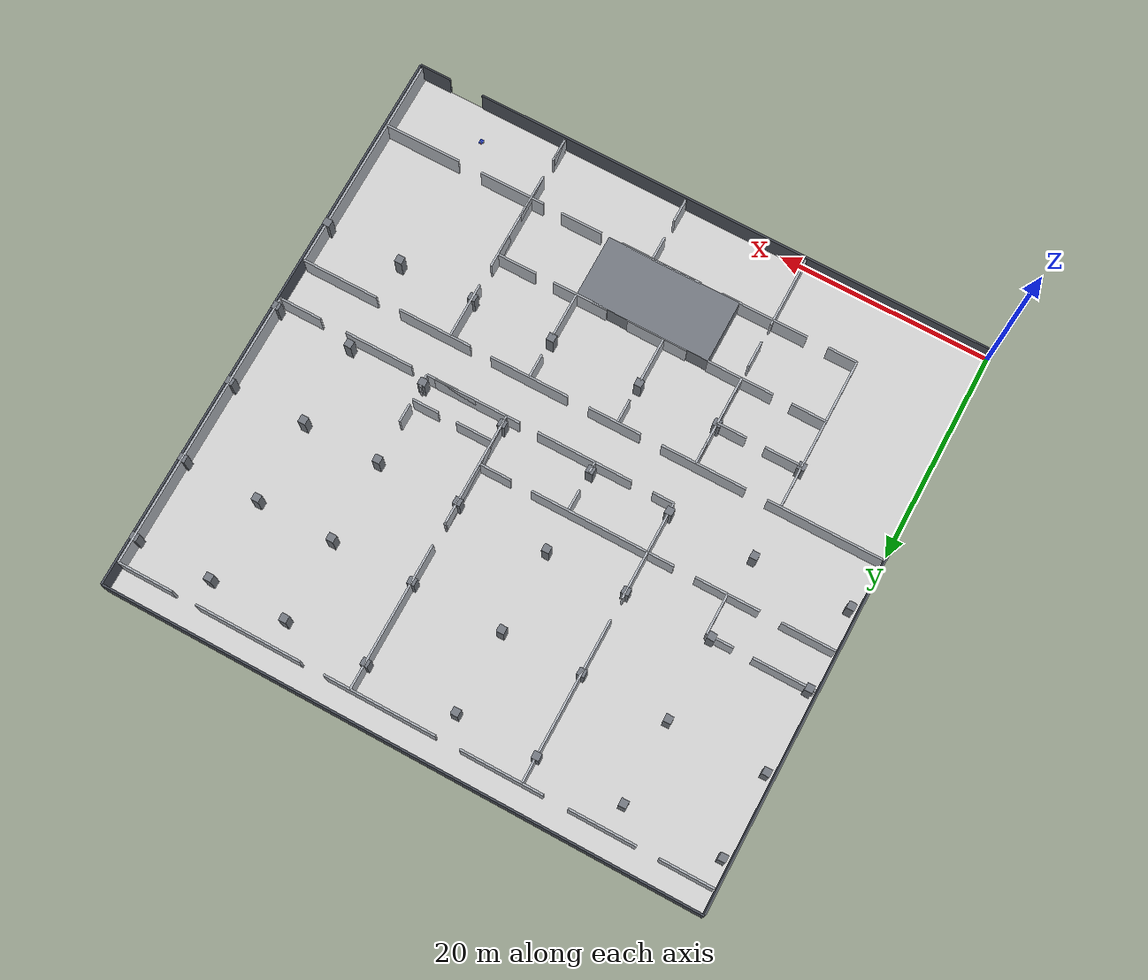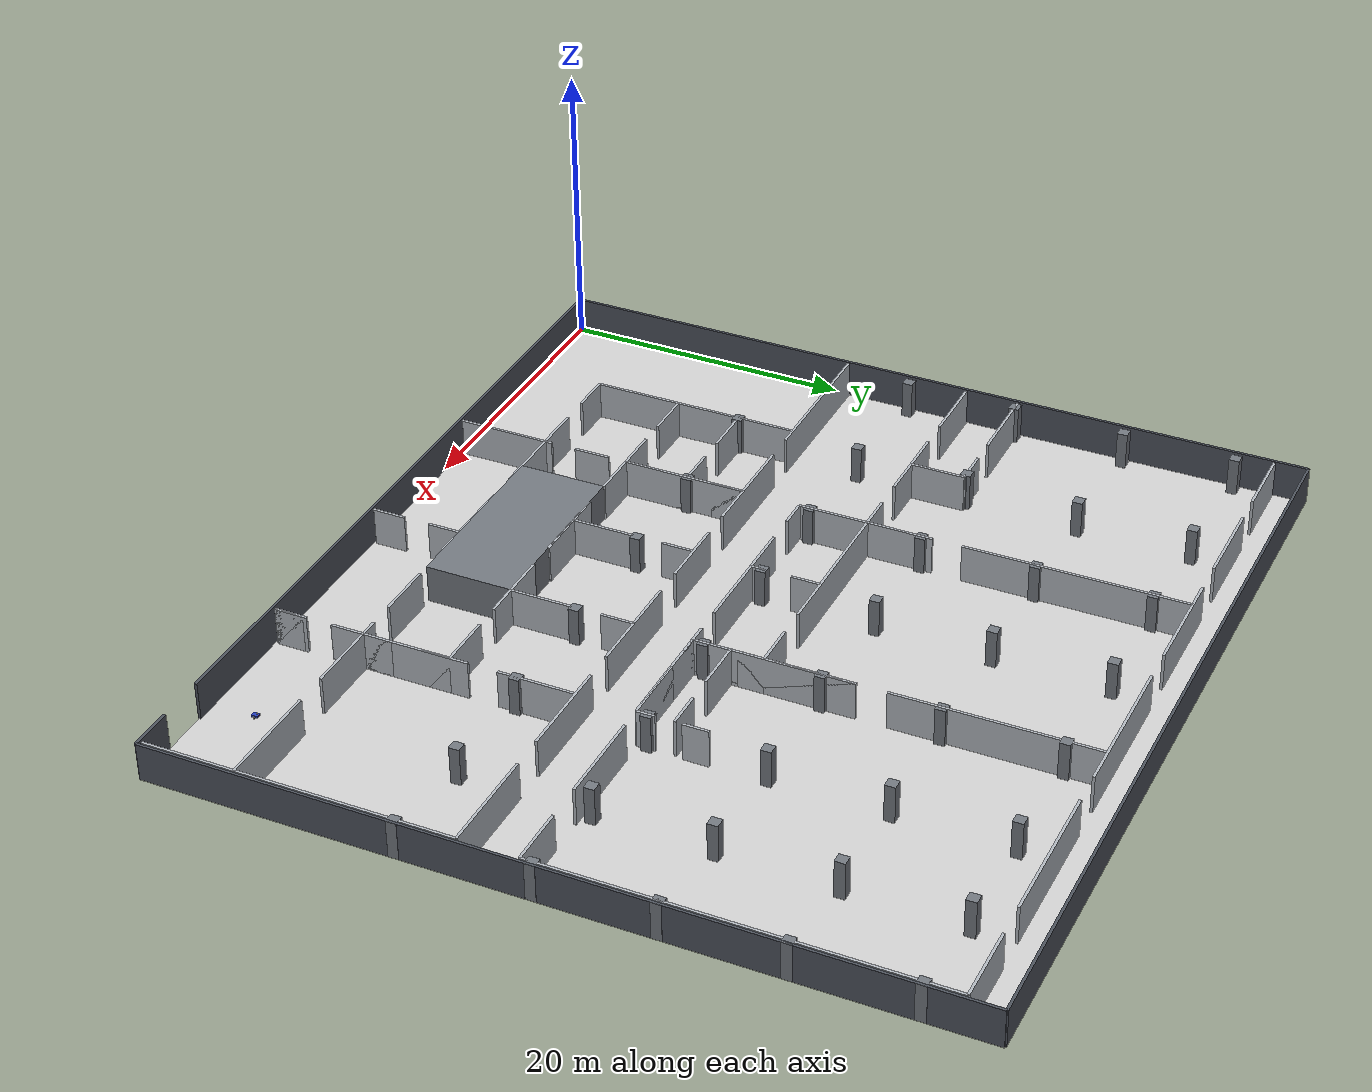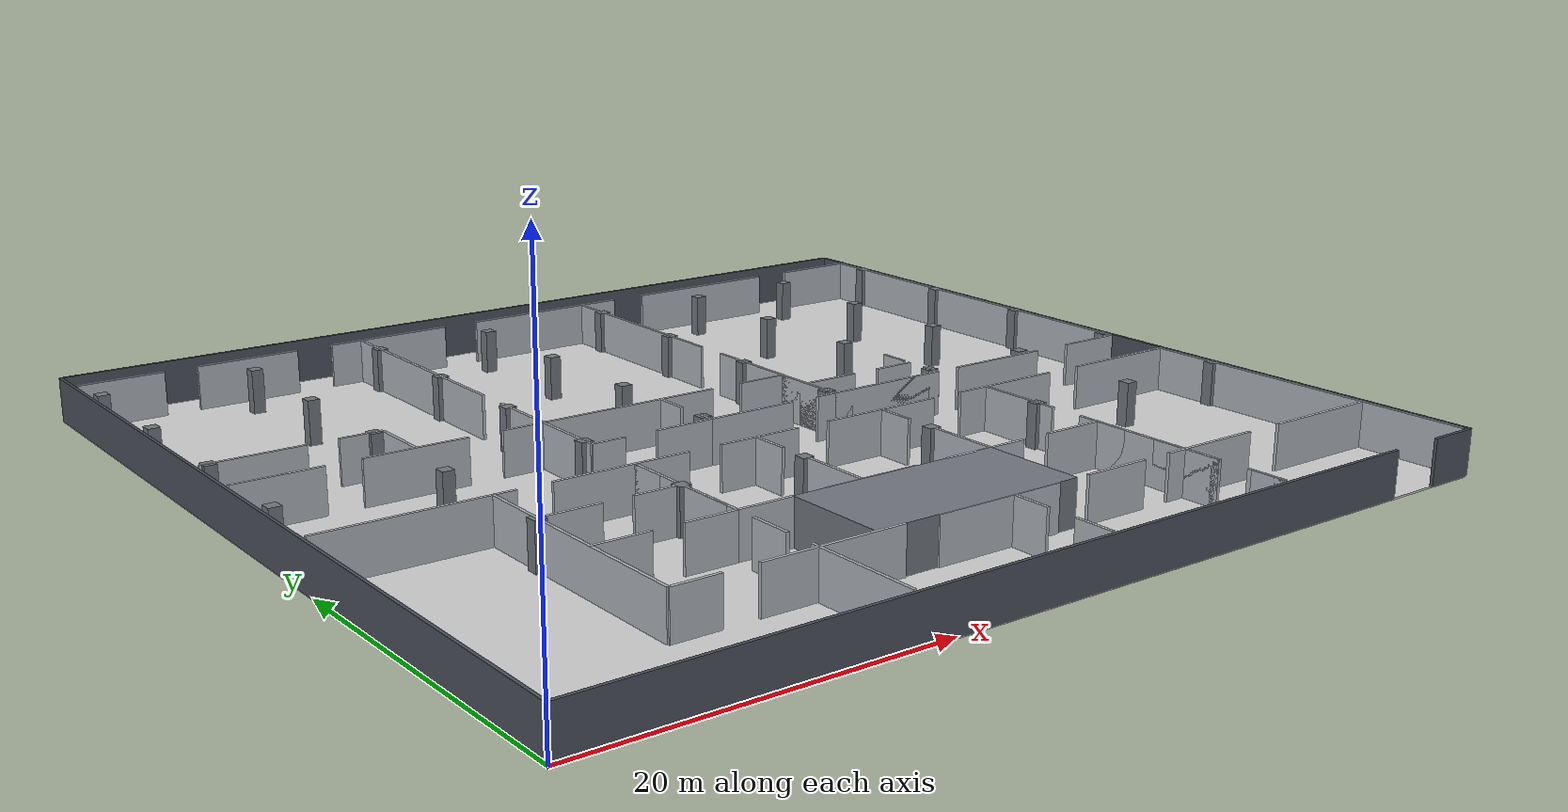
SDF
<?xml version="1.0" ?>
<sdf version="1.8">
  <world name="osco_scenario_world">

    <physics name="1ms" type="ignored">
      <max_step_size>0.001</max_step_size>
      <real_time_factor>1.0</real_time_factor>
    </physics>

    <plugin
      filename="gz-sim-physics-system"
      name="gz::sim::systems::Physics">
    </plugin>

    <plugin
      filename="gz-sim-user-commands-system"
      name="gz::sim::systems::UserCommands">
    </plugin>

    <plugin
      filename="gz-sim-scene-broadcaster-system"
      name="gz::sim::systems::SceneBroadcaster">
    </plugin>

    <!-- FIRE_SWARM_SENSORS_SYSTEM_BEGIN -->
    <plugin
      filename="gz-sim-sensors-system"
      name="gz::sim::systems::Sensors">
      <render_engine>ogre2</render_engine>
    </plugin>
    <!-- FIRE_SWARM_SENSORS_SYSTEM_END -->

    <scene>
      <ambient>0.65 0.65 0.65 1</ambient>
      <background>0.85 0.88 0.92 1</background>
      <shadows>true</shadows>
    </scene>

    <light type="directional" name="sun">
      <cast_shadows>true</cast_shadows>
      <pose>0 0 20 0 0 0</pose>
      <diffuse>0.9 0.9 0.9 1</diffuse>
      <specular>0.2 0.2 0.2 1</specular>
      <attenuation>
        <range>1000</range>
        <constant>0.9</constant>
        <linear>0.01</linear>
        <quadratic>0.001</quadratic>
      </attenuation>
      <direction>-0.5 0.1 -0.9</direction>
    </light>

    <model name="osco_floor">
      <static>true</static>
      <link name="floor_link">
        <collision name="floor_collision">
          <pose>28.1250 26.8750 -0.0500 0 0 0</pose>
          <geometry>
            <box>
              <size>56.2500 53.7500 0.1000</size>
            </box>
          </geometry>
        </collision>
        <visual name="floor_visual">
          <pose>28.1250 26.8750 -0.0500 0 0 0</pose>
          <geometry>
            <box>
              <size>56.2500 53.7500 0.1000</size>
            </box>
          </geometry>
          <material>
            <ambient>0.82 0.82 0.82 1</ambient>
            <diffuse>0.82 0.82 0.82 1</diffuse>
          </material>
        </visual>
      </link>
    </model>

    <model name="osco_static_structure">
      <static>true</static>
      <link name="structure_link">

      <collision name="upper_corridor_south_0_collision">
        <pose>2.7500 51.5000 1.3000 0 0 0</pose>
        <geometry>
          <box>
            <size>5.0000 0.1800 2.6000</size>
          </box>
        </geometry>
      </collision>

      <visual name="upper_corridor_south_0_visual">
        <pose>2.7500 51.5000 1.3000 0 0 0</pose>
        <geometry>
          <box>
            <size>5.0000 0.1800 2.6000</size>
          </box>
        </geometry>
        <material>
          <ambient>0.700 0.720 0.750 1.000</ambient>
          <diffuse>0.700 0.720 0.750 1.000</diffuse>
        </material>
      </visual>

      <collision name="upper_corridor_south_1_collision">
        <pose>10.3750 51.5000 1.3000 0 0 0</pose>
        <geometry>
          <box>
            <size>6.2500 0.1800 2.6000</size>
          </box>
        </geometry>
      </collision>

      <visual name="upper_corridor_south_1_visual">
        <pose>10.3750 51.5000 1.3000 0 0 0</pose>
        <geometry>
          <box>
            <size>6.2500 0.1800 2.6000</size>
          </box>
        </geometry>
        <material>
          <ambient>0.700 0.720 0.750 1.000</ambient>
          <diffuse>0.700 0.720 0.750 1.000</diffuse>
        </material>
      </visual>

      <collision name="upper_corridor_south_2_collision">
        <pose>19.6250 51.5000 1.3000 0 0 0</pose>
        <geometry>
          <box>
            <size>7.7500 0.1800 2.6000</size>
          </box>
        </geometry>
      </collision>

      <visual name="upper_corridor_south_2_visual">
        <pose>19.6250 51.5000 1.3000 0 0 0</pose>
        <geometry>
          <box>
            <size>7.7500 0.1800 2.6000</size>
          </box>
        </geometry>
        <material>
          <ambient>0.700 0.720 0.750 1.000</ambient>
          <diffuse>0.700 0.720 0.750 1.000</diffuse>
        </material>
      </visual>

      <collision name="upper_corridor_south_3_collision">
        <pose>31.0000 51.5000 1.3000 0 0 0</pose>
        <geometry>
          <box>
            <size>10.5000 0.1800 2.6000</size>
          </box>
        </geometry>
      </collision>

      <visual name="upper_corridor_south_3_visual">
        <pose>31.0000 51.5000 1.3000 0 0 0</pose>
        <geometry>
          <box>
            <size>10.5000 0.1800 2.6000</size>
          </box>
        </geometry>
        <material>
          <ambient>0.700 0.720 0.750 1.000</ambient>
          <diffuse>0.700 0.720 0.750 1.000</diffuse>
        </material>
      </visual>

      <collision name="upper_corridor_south_4_collision">
        <pose>43.5000 51.5000 1.3000 0 0 0</pose>
        <geometry>
          <box>
            <size>10.0000 0.1800 2.6000</size>
          </box>
        </geometry>
      </collision>

      <visual name="upper_corridor_south_4_visual">
        <pose>43.5000 51.5000 1.3000 0 0 0</pose>
        <geometry>
          <box>
            <size>10.0000 0.1800 2.6000</size>
          </box>
        </geometry>
        <material>
          <ambient>0.700 0.720 0.750 1.000</ambient>
          <diffuse>0.700 0.720 0.750 1.000</diffuse>
        </material>
      </visual>

      <collision name="upper_corridor_south_5_collision">
        <pose>53.3750 51.5000 1.3000 0 0 0</pose>
        <geometry>
          <box>
            <size>5.2500 0.1800 2.6000</size>
          </box>
        </geometry>
      </collision>

      <visual name="upper_corridor_south_5_visual">
        <pose>53.3750 51.5000 1.3000 0 0 0</pose>
        <geometry>
          <box>
            <size>5.2500 0.1800 2.6000</size>
          </box>
        </geometry>
        <material>
          <ambient>0.700 0.720 0.750 1.000</ambient>
          <diffuse>0.700 0.720 0.750 1.000</diffuse>
        </material>
      </visual>

      <collision name="operator_east_0_collision">
        <pose>17.7500 43.8750 1.3000 0 0 0</pose>
        <geometry>
          <box>
            <size>0.1800 15.2500 2.6000</size>
          </box>
        </geometry>
      </collision>

      <visual name="operator_east_0_visual">
        <pose>17.7500 43.8750 1.3000 0 0 0</pose>
        <geometry>
          <box>
            <size>0.1800 15.2500 2.6000</size>
          </box>
        </geometry>
        <material>
          <ambient>0.700 0.720 0.750 1.000</ambient>
          <diffuse>0.700 0.720 0.750 1.000</diffuse>
        </material>
      </visual>

      <collision name="operator_east_1_collision">
        <pose>17.7500 32.0000 1.3000 0 0 0</pose>
        <geometry>
          <box>
            <size>0.1800 4.5000 2.6000</size>
          </box>
        </geometry>
      </collision>

      <visual name="operator_east_1_visual">
        <pose>17.7500 32.0000 1.3000 0 0 0</pose>
        <geometry>
          <box>
            <size>0.1800 4.5000 2.6000</size>
          </box>
        </geometry>
        <material>
          <ambient>0.700 0.720 0.750 1.000</ambient>
          <diffuse>0.700 0.720 0.750 1.000</diffuse>
        </material>
      </visual>

      <collision name="operator_south_0_collision">
        <pose>2.7500 29.7500 1.3000 0 0 0</pose>
        <geometry>
          <box>
            <size>5.0000 0.1800 2.6000</size>
          </box>
        </geometry>
      </collision>

      <visual name="operator_south_0_visual">
        <pose>2.7500 29.7500 1.3000 0 0 0</pose>
        <geometry>
          <box>
            <size>5.0000 0.1800 2.6000</size>
          </box>
        </geometry>
        <material>
          <ambient>0.700 0.720 0.750 1.000</ambient>
          <diffuse>0.700 0.720 0.750 1.000</diffuse>
        </material>
      </visual>

      <collision name="operator_south_1_collision">
        <pose>10.2500 29.7500 1.3000 0 0 0</pose>
        <geometry>
          <box>
            <size>6.0000 0.1800 2.6000</size>
          </box>
        </geometry>
      </collision>

      <visual name="operator_south_1_visual">
        <pose>10.2500 29.7500 1.3000 0 0 0</pose>
        <geometry>
          <box>
            <size>6.0000 0.1800 2.6000</size>
          </box>
        </geometry>
        <material>
          <ambient>0.700 0.720 0.750 1.000</ambient>
          <diffuse>0.700 0.720 0.750 1.000</diffuse>
        </material>
      </visual>

      <collision name="operator_south_2_collision">
        <pose>16.5000 29.7500 1.3000 0 0 0</pose>
        <geometry>
          <box>
            <size>2.5000 0.1800 2.6000</size>
          </box>
        </geometry>
      </collision>

      <visual name="operator_south_2_visual">
        <pose>16.5000 29.7500 1.3000 0 0 0</pose>
        <geometry>
          <box>
            <size>2.5000 0.1800 2.6000</size>
          </box>
        </geometry>
        <material>
          <ambient>0.700 0.720 0.750 1.000</ambient>
          <diffuse>0.700 0.720 0.750 1.000</diffuse>
        </material>
      </visual>

      <collision name="meeting_north_0_collision">
        <pose>3.1250 33.5000 1.3000 0 0 0</pose>
        <geometry>
          <box>
            <size>5.7500 0.1800 2.6000</size>
          </box>
        </geometry>
      </collision>

      <visual name="meeting_north_0_visual">
        <pose>3.1250 33.5000 1.3000 0 0 0</pose>
        <geometry>
          <box>
            <size>5.7500 0.1800 2.6000</size>
          </box>
        </geometry>
        <material>
          <ambient>0.700 0.720 0.750 1.000</ambient>
          <diffuse>0.700 0.720 0.750 1.000</diffuse>
        </material>
      </visual>

      <collision name="meeting_north_1_collision">
        <pose>9.0000 33.5000 1.3000 0 0 0</pose>
        <geometry>
          <box>
            <size>2.5000 0.1800 2.6000</size>
          </box>
        </geometry>
      </collision>

      <visual name="meeting_north_1_visual">
        <pose>9.0000 33.5000 1.3000 0 0 0</pose>
        <geometry>
          <box>
            <size>2.5000 0.1800 2.6000</size>
          </box>
        </geometry>
        <material>
          <ambient>0.700 0.720 0.750 1.000</ambient>
          <diffuse>0.700 0.720 0.750 1.000</diffuse>
        </material>
      </visual>

      <collision name="meeting_east_0_collision">
        <pose>10.2500 31.6250 1.3000 0 0 0</pose>
        <geometry>
          <box>
            <size>0.1800 3.7500 2.6000</size>
          </box>
        </geometry>
      </collision>

      <visual name="meeting_east_0_visual">
        <pose>10.2500 31.6250 1.3000 0 0 0</pose>
        <geometry>
          <box>
            <size>0.1800 3.7500 2.6000</size>
          </box>
        </geometry>
        <material>
          <ambient>0.700 0.720 0.750 1.000</ambient>
          <diffuse>0.700 0.720 0.750 1.000</diffuse>
        </material>
      </visual>

      <collision name="catering_west_0_collision">
        <pose>17.7500 43.8750 1.3000 0 0 0</pose>
        <geometry>
          <box>
            <size>0.1800 15.2500 2.6000</size>
          </box>
        </geometry>
      </collision>

      <visual name="catering_west_0_visual">
        <pose>17.7500 43.8750 1.3000 0 0 0</pose>
        <geometry>
          <box>
            <size>0.1800 15.2500 2.6000</size>
          </box>
        </geometry>
        <material>
          <ambient>0.700 0.720 0.750 1.000</ambient>
          <diffuse>0.700 0.720 0.750 1.000</diffuse>
        </material>
      </visual>

      <collision name="catering_west_1_collision">
        <pose>17.7500 32.0000 1.3000 0 0 0</pose>
        <geometry>
          <box>
            <size>0.1800 4.5000 2.6000</size>
          </box>
        </geometry>
      </collision>

      <visual name="catering_west_1_visual">
        <pose>17.7500 32.0000 1.3000 0 0 0</pose>
        <geometry>
          <box>
            <size>0.1800 4.5000 2.6000</size>
          </box>
        </geometry>
        <material>
          <ambient>0.700 0.720 0.750 1.000</ambient>
          <diffuse>0.700 0.720 0.750 1.000</diffuse>
        </material>
      </visual>

      <collision name="catering_east_0_collision">
        <pose>33.7500 44.6250 1.3000 0 0 0</pose>
        <geometry>
          <box>
            <size>0.1800 13.7500 2.6000</size>
          </box>
        </geometry>
      </collision>

      <visual name="catering_east_0_visual">
        <pose>33.7500 44.6250 1.3000 0 0 0</pose>
        <geometry>
          <box>
            <size>0.1800 13.7500 2.6000</size>
          </box>
        </geometry>
        <material>
          <ambient>0.700 0.720 0.750 1.000</ambient>
          <diffuse>0.700 0.720 0.750 1.000</diffuse>
        </material>
      </visual>

      <collision name="catering_east_1_collision">
        <pose>33.7500 32.7500 1.3000 0 0 0</pose>
        <geometry>
          <box>
            <size>0.1800 6.0000 2.6000</size>
          </box>
        </geometry>
      </collision>

      <visual name="catering_east_1_visual">
        <pose>33.7500 32.7500 1.3000 0 0 0</pose>
        <geometry>
          <box>
            <size>0.1800 6.0000 2.6000</size>
          </box>
        </geometry>
        <material>
          <ambient>0.700 0.720 0.750 1.000</ambient>
          <diffuse>0.700 0.720 0.750 1.000</diffuse>
        </material>
      </visual>

      <collision name="catering_south_0_collision">
        <pose>23.2500 29.7500 1.3000 0 0 0</pose>
        <geometry>
          <box>
            <size>11.0000 0.1800 2.6000</size>
          </box>
        </geometry>
      </collision>

      <visual name="catering_south_0_visual">
        <pose>23.2500 29.7500 1.3000 0 0 0</pose>
        <geometry>
          <box>
            <size>11.0000 0.1800 2.6000</size>
          </box>
        </geometry>
        <material>
          <ambient>0.700 0.720 0.750 1.000</ambient>
          <diffuse>0.700 0.720 0.750 1.000</diffuse>
        </material>
      </visual>

      <collision name="catering_south_1_collision">
        <pose>32.2500 29.7500 1.3000 0 0 0</pose>
        <geometry>
          <box>
            <size>3.0000 0.1800 2.6000</size>
          </box>
        </geometry>
      </collision>

      <visual name="catering_south_1_visual">
        <pose>32.2500 29.7500 1.3000 0 0 0</pose>
        <geometry>
          <box>
            <size>3.0000 0.1800 2.6000</size>
          </box>
        </geometry>
        <material>
          <ambient>0.700 0.720 0.750 1.000</ambient>
          <diffuse>0.700 0.720 0.750 1.000</diffuse>
        </material>
      </visual>

      <collision name="museum_west_0_collision">
        <pose>33.7500 44.6250 1.3000 0 0 0</pose>
        <geometry>
          <box>
            <size>0.1800 13.7500 2.6000</size>
          </box>
        </geometry>
      </collision>

      <visual name="museum_west_0_visual">
        <pose>33.7500 44.6250 1.3000 0 0 0</pose>
        <geometry>
          <box>
            <size>0.1800 13.7500 2.6000</size>
          </box>
        </geometry>
        <material>
          <ambient>0.700 0.720 0.750 1.000</ambient>
          <diffuse>0.700 0.720 0.750 1.000</diffuse>
        </material>
      </visual>

      <collision name="museum_west_1_collision">
        <pose>33.7500 30.3750 1.3000 0 0 0</pose>
        <geometry>
          <box>
            <size>0.1800 10.7500 2.6000</size>
          </box>
        </geometry>
      </collision>

      <visual name="museum_west_1_visual">
        <pose>33.7500 30.3750 1.3000 0 0 0</pose>
        <geometry>
          <box>
            <size>0.1800 10.7500 2.6000</size>
          </box>
        </geometry>
        <material>
          <ambient>0.700 0.720 0.750 1.000</ambient>
          <diffuse>0.700 0.720 0.750 1.000</diffuse>
        </material>
      </visual>

      <collision name="museum_east_0_collision">
        <pose>56.0000 38.2500 1.3000 0 0 0</pose>
        <geometry>
          <box>
            <size>0.1800 26.5000 2.6000</size>
          </box>
        </geometry>
      </collision>

      <visual name="museum_east_0_visual">
        <pose>56.0000 38.2500 1.3000 0 0 0</pose>
        <geometry>
          <box>
            <size>0.1800 26.5000 2.6000</size>
          </box>
        </geometry>
        <material>
          <ambient>0.700 0.720 0.750 1.000</ambient>
          <diffuse>0.700 0.720 0.750 1.000</diffuse>
        </material>
      </visual>

      <collision name="museum_south_0_collision">
        <pose>37.2500 25.0000 1.3000 0 0 0</pose>
        <geometry>
          <box>
            <size>7.0000 0.1800 2.6000</size>
          </box>
        </geometry>
      </collision>

      <visual name="museum_south_0_visual">
        <pose>37.2500 25.0000 1.3000 0 0 0</pose>
        <geometry>
          <box>
            <size>7.0000 0.1800 2.6000</size>
          </box>
        </geometry>
        <material>
          <ambient>0.700 0.720 0.750 1.000</ambient>
          <diffuse>0.700 0.720 0.750 1.000</diffuse>
        </material>
      </visual>

      <collision name="museum_south_1_collision">
        <pose>46.2500 25.0000 1.3000 0 0 0</pose>
        <geometry>
          <box>
            <size>6.5000 0.1800 2.6000</size>
          </box>
        </geometry>
      </collision>

      <visual name="museum_south_1_visual">
        <pose>46.2500 25.0000 1.3000 0 0 0</pose>
        <geometry>
          <box>
            <size>6.5000 0.1800 2.6000</size>
          </box>
        </geometry>
        <material>
          <ambient>0.700 0.720 0.750 1.000</ambient>
          <diffuse>0.700 0.720 0.750 1.000</diffuse>
        </material>
      </visual>

      <collision name="museum_south_2_collision">
        <pose>54.0000 25.0000 1.3000 0 0 0</pose>
        <geometry>
          <box>
            <size>4.0000 0.1800 2.6000</size>
          </box>
        </geometry>
      </collision>

      <visual name="museum_south_2_visual">
        <pose>54.0000 25.0000 1.3000 0 0 0</pose>
        <geometry>
          <box>
            <size>4.0000 0.1800 2.6000</size>
          </box>
        </geometry>
        <material>
          <ambient>0.700 0.720 0.750 1.000</ambient>
          <diffuse>0.700 0.720 0.750 1.000</diffuse>
        </material>
      </visual>

      <collision name="storage4_west_0_collision">
        <pose>17.7500 27.3750 1.3000 0 0 0</pose>
        <geometry>
          <box>
            <size>0.1800 4.7500 2.6000</size>
          </box>
        </geometry>
      </collision>

      <visual name="storage4_west_0_visual">
        <pose>17.7500 27.3750 1.3000 0 0 0</pose>
        <geometry>
          <box>
            <size>0.1800 4.7500 2.6000</size>
          </box>
        </geometry>
        <material>
          <ambient>0.700 0.720 0.750 1.000</ambient>
          <diffuse>0.700 0.720 0.750 1.000</diffuse>
        </material>
      </visual>

      <collision name="storage4_east_0_collision">
        <pose>25.2500 28.7500 1.3000 0 0 0</pose>
        <geometry>
          <box>
            <size>0.1800 2.0000 2.6000</size>
          </box>
        </geometry>
      </collision>

      <visual name="storage4_east_0_visual">
        <pose>25.2500 28.7500 1.3000 0 0 0</pose>
        <geometry>
          <box>
            <size>0.1800 2.0000 2.6000</size>
          </box>
        </geometry>
        <material>
          <ambient>0.700 0.720 0.750 1.000</ambient>
          <diffuse>0.700 0.720 0.750 1.000</diffuse>
        </material>
      </visual>

      <collision name="storage4_east_1_collision">
        <pose>25.2500 25.5000 1.3000 0 0 0</pose>
        <geometry>
          <box>
            <size>0.1800 1.0000 2.6000</size>
          </box>
        </geometry>
      </collision>

      <visual name="storage4_east_1_visual">
        <pose>25.2500 25.5000 1.3000 0 0 0</pose>
        <geometry>
          <box>
            <size>0.1800 1.0000 2.6000</size>
          </box>
        </geometry>
        <material>
          <ambient>0.700 0.720 0.750 1.000</ambient>
          <diffuse>0.700 0.720 0.750 1.000</diffuse>
        </material>
      </visual>

      <collision name="storage4_south_0_collision">
        <pose>18.7500 25.0000 1.3000 0 0 0</pose>
        <geometry>
          <box>
            <size>2.0000 0.1800 2.6000</size>
          </box>
        </geometry>
      </collision>

      <visual name="storage4_south_0_visual">
        <pose>18.7500 25.0000 1.3000 0 0 0</pose>
        <geometry>
          <box>
            <size>2.0000 0.1800 2.6000</size>
          </box>
        </geometry>
        <material>
          <ambient>0.700 0.720 0.750 1.000</ambient>
          <diffuse>0.700 0.720 0.750 1.000</diffuse>
        </material>
      </visual>

      <collision name="storage4_south_1_collision">
        <pose>23.5000 25.0000 1.3000 0 0 0</pose>
        <geometry>
          <box>
            <size>3.5000 0.1800 2.6000</size>
          </box>
        </geometry>
      </collision>

      <visual name="storage4_south_1_visual">
        <pose>23.5000 25.0000 1.3000 0 0 0</pose>
        <geometry>
          <box>
            <size>3.5000 0.1800 2.6000</size>
          </box>
        </geometry>
        <material>
          <ambient>0.700 0.720 0.750 1.000</ambient>
          <diffuse>0.700 0.720 0.750 1.000</diffuse>
        </material>
      </visual>

      <collision name="service_east_0_collision">
        <pose>33.7500 28.8750 1.3000 0 0 0</pose>
        <geometry>
          <box>
            <size>0.1800 1.7500 2.6000</size>
          </box>
        </geometry>
      </collision>

      <visual name="service_east_0_visual">
        <pose>33.7500 28.8750 1.3000 0 0 0</pose>
        <geometry>
          <box>
            <size>0.1800 1.7500 2.6000</size>
          </box>
        </geometry>
        <material>
          <ambient>0.700 0.720 0.750 1.000</ambient>
          <diffuse>0.700 0.720 0.750 1.000</diffuse>
        </material>
      </visual>

      <collision name="service_east_1_collision">
        <pose>33.7500 25.5000 1.3000 0 0 0</pose>
        <geometry>
          <box>
            <size>0.1800 1.0000 2.6000</size>
          </box>
        </geometry>
      </collision>

      <visual name="service_east_1_visual">
        <pose>33.7500 25.5000 1.3000 0 0 0</pose>
        <geometry>
          <box>
            <size>0.1800 1.0000 2.6000</size>
          </box>
        </geometry>
        <material>
          <ambient>0.700 0.720 0.750 1.000</ambient>
          <diffuse>0.700 0.720 0.750 1.000</diffuse>
        </material>
      </visual>

      <collision name="service_south_0_collision">
        <pose>28.0000 25.0000 1.3000 0 0 0</pose>
        <geometry>
          <box>
            <size>5.5000 0.1800 2.6000</size>
          </box>
        </geometry>
      </collision>

      <visual name="service_south_0_visual">
        <pose>28.0000 25.0000 1.3000 0 0 0</pose>
        <geometry>
          <box>
            <size>5.5000 0.1800 2.6000</size>
          </box>
        </geometry>
        <material>
          <ambient>0.700 0.720 0.750 1.000</ambient>
          <diffuse>0.700 0.720 0.750 1.000</diffuse>
        </material>
      </visual>

      <collision name="service_south_1_collision">
        <pose>33.1250 25.0000 1.3000 0 0 0</pose>
        <geometry>
          <box>
            <size>1.2500 0.1800 2.6000</size>
          </box>
        </geometry>
      </collision>

      <visual name="service_south_1_visual">
        <pose>33.1250 25.0000 1.3000 0 0 0</pose>
        <geometry>
          <box>
            <size>1.2500 0.1800 2.6000</size>
          </box>
        </geometry>
        <material>
          <ambient>0.700 0.720 0.750 1.000</ambient>
          <diffuse>0.700 0.720 0.750 1.000</diffuse>
        </material>
      </visual>

      <collision name="mdf_west_0_collision">
        <pose>33.7500 27.3750 1.3000 0 0 0</pose>
        <geometry>
          <box>
            <size>0.1800 4.7500 2.6000</size>
          </box>
        </geometry>
      </collision>

      <visual name="mdf_west_0_visual">
        <pose>33.7500 27.3750 1.3000 0 0 0</pose>
        <geometry>
          <box>
            <size>0.1800 4.7500 2.6000</size>
          </box>
        </geometry>
        <material>
          <ambient>0.700 0.720 0.750 1.000</ambient>
          <diffuse>0.700 0.720 0.750 1.000</diffuse>
        </material>
      </visual>

      <collision name="storage3_east_0_collision">
        <pose>41.5000 28.8750 1.3000 0 0 0</pose>
        <geometry>
          <box>
            <size>0.1800 1.7500 2.6000</size>
          </box>
        </geometry>
      </collision>

      <visual name="storage3_east_0_visual">
        <pose>41.5000 28.8750 1.3000 0 0 0</pose>
        <geometry>
          <box>
            <size>0.1800 1.7500 2.6000</size>
          </box>
        </geometry>
        <material>
          <ambient>0.700 0.720 0.750 1.000</ambient>
          <diffuse>0.700 0.720 0.750 1.000</diffuse>
        </material>
      </visual>

      <collision name="storage3_east_1_collision">
        <pose>41.5000 25.6250 1.3000 0 0 0</pose>
        <geometry>
          <box>
            <size>0.1800 1.2500 2.6000</size>
          </box>
        </geometry>
      </collision>

      <visual name="storage3_east_1_visual">
        <pose>41.5000 25.6250 1.3000 0 0 0</pose>
        <geometry>
          <box>
            <size>0.1800 1.2500 2.6000</size>
          </box>
        </geometry>
        <material>
          <ambient>0.700 0.720 0.750 1.000</ambient>
          <diffuse>0.700 0.720 0.750 1.000</diffuse>
        </material>
      </visual>

      <collision name="mdf_storage_divider_0_collision">
        <pose>35.5000 27.5000 1.3000 0 0 0</pose>
        <geometry>
          <box>
            <size>3.5000 0.1800 2.6000</size>
          </box>
        </geometry>
      </collision>

      <visual name="mdf_storage_divider_0_visual">
        <pose>35.5000 27.5000 1.3000 0 0 0</pose>
        <geometry>
          <box>
            <size>3.5000 0.1800 2.6000</size>
          </box>
        </geometry>
        <material>
          <ambient>0.700 0.720 0.750 1.000</ambient>
          <diffuse>0.700 0.720 0.750 1.000</diffuse>
        </material>
      </visual>

      <collision name="mdf_storage_divider_1_collision">
        <pose>40.2500 27.5000 1.3000 0 0 0</pose>
        <geometry>
          <box>
            <size>2.5000 0.1800 2.6000</size>
          </box>
        </geometry>
      </collision>

      <visual name="mdf_storage_divider_1_visual">
        <pose>40.2500 27.5000 1.3000 0 0 0</pose>
        <geometry>
          <box>
            <size>2.5000 0.1800 2.6000</size>
          </box>
        </geometry>
        <material>
          <ambient>0.700 0.720 0.750 1.000</ambient>
          <diffuse>0.700 0.720 0.750 1.000</diffuse>
        </material>
      </visual>

      <collision name="storage3_south_0_collision">
        <pose>34.3750 25.0000 1.3000 0 0 0</pose>
        <geometry>
          <box>
            <size>1.2500 0.1800 2.6000</size>
          </box>
        </geometry>
      </collision>

      <visual name="storage3_south_0_visual">
        <pose>34.3750 25.0000 1.3000 0 0 0</pose>
        <geometry>
          <box>
            <size>1.2500 0.1800 2.6000</size>
          </box>
        </geometry>
        <material>
          <ambient>0.700 0.720 0.750 1.000</ambient>
          <diffuse>0.700 0.720 0.750 1.000</diffuse>
        </material>
      </visual>

      <collision name="storage3_south_1_collision">
        <pose>39.1250 25.0000 1.3000 0 0 0</pose>
        <geometry>
          <box>
            <size>4.7500 0.1800 2.6000</size>
          </box>
        </geometry>
      </collision>

      <visual name="storage3_south_1_visual">
        <pose>39.1250 25.0000 1.3000 0 0 0</pose>
        <geometry>
          <box>
            <size>4.7500 0.1800 2.6000</size>
          </box>
        </geometry>
        <material>
          <ambient>0.700 0.720 0.750 1.000</ambient>
          <diffuse>0.700 0.720 0.750 1.000</diffuse>
        </material>
      </visual>

      <collision name="middle_corridor_south_0_collision">
        <pose>5.6250 21.0000 1.3000 0 0 0</pose>
        <geometry>
          <box>
            <size>10.7500 0.1800 2.6000</size>
          </box>
        </geometry>
      </collision>

      <visual name="middle_corridor_south_0_visual">
        <pose>5.6250 21.0000 1.3000 0 0 0</pose>
        <geometry>
          <box>
            <size>10.7500 0.1800 2.6000</size>
          </box>
        </geometry>
        <material>
          <ambient>0.700 0.720 0.750 1.000</ambient>
          <diffuse>0.700 0.720 0.750 1.000</diffuse>
        </material>
      </visual>

      <collision name="middle_corridor_south_1_collision">
        <pose>17.0000 21.0000 1.3000 0 0 0</pose>
        <geometry>
          <box>
            <size>8.0000 0.1800 2.6000</size>
          </box>
        </geometry>
      </collision>

      <visual name="middle_corridor_south_1_visual">
        <pose>17.0000 21.0000 1.3000 0 0 0</pose>
        <geometry>
          <box>
            <size>8.0000 0.1800 2.6000</size>
          </box>
        </geometry>
        <material>
          <ambient>0.700 0.720 0.750 1.000</ambient>
          <diffuse>0.700 0.720 0.750 1.000</diffuse>
        </material>
      </visual>

      <collision name="middle_corridor_south_2_collision">
        <pose>25.5000 21.0000 1.3000 0 0 0</pose>
        <geometry>
          <box>
            <size>5.0000 0.1800 2.6000</size>
          </box>
        </geometry>
      </collision>

      <visual name="middle_corridor_south_2_visual">
        <pose>25.5000 21.0000 1.3000 0 0 0</pose>
        <geometry>
          <box>
            <size>5.0000 0.1800 2.6000</size>
          </box>
        </geometry>
        <material>
          <ambient>0.700 0.720 0.750 1.000</ambient>
          <diffuse>0.700 0.720 0.750 1.000</diffuse>
        </material>
      </visual>

      <collision name="middle_corridor_south_3_collision">
        <pose>33.7500 21.0000 1.3000 0 0 0</pose>
        <geometry>
          <box>
            <size>7.5000 0.1800 2.6000</size>
          </box>
        </geometry>
      </collision>

      <visual name="middle_corridor_south_3_visual">
        <pose>33.7500 21.0000 1.3000 0 0 0</pose>
        <geometry>
          <box>
            <size>7.5000 0.1800 2.6000</size>
          </box>
        </geometry>
        <material>
          <ambient>0.700 0.720 0.750 1.000</ambient>
          <diffuse>0.700 0.720 0.750 1.000</diffuse>
        </material>
      </visual>

      <collision name="middle_corridor_south_4_collision">
        <pose>43.0000 21.0000 1.3000 0 0 0</pose>
        <geometry>
          <box>
            <size>7.0000 0.1800 2.6000</size>
          </box>
        </geometry>
      </collision>

      <visual name="middle_corridor_south_4_visual">
        <pose>43.0000 21.0000 1.3000 0 0 0</pose>
        <geometry>
          <box>
            <size>7.0000 0.1800 2.6000</size>
          </box>
        </geometry>
        <material>
          <ambient>0.700 0.720 0.750 1.000</ambient>
          <diffuse>0.700 0.720 0.750 1.000</diffuse>
        </material>
      </visual>

      <collision name="middle_corridor_south_5_collision">
        <pose>52.3750 21.0000 1.3000 0 0 0</pose>
        <geometry>
          <box>
            <size>7.2500 0.1800 2.6000</size>
          </box>
        </geometry>
      </collision>

      <visual name="middle_corridor_south_5_visual">
        <pose>52.3750 21.0000 1.3000 0 0 0</pose>
        <geometry>
          <box>
            <size>7.2500 0.1800 2.6000</size>
          </box>
        </geometry>
        <material>
          <ambient>0.700 0.720 0.750 1.000</ambient>
          <diffuse>0.700 0.720 0.750 1.000</diffuse>
        </material>
      </visual>

      <collision name="vip_block_west_0_collision">
        <pose>9.7500 13.7500 1.3000 0 0 0</pose>
        <geometry>
          <box>
            <size>0.1800 14.5000 2.6000</size>
          </box>
        </geometry>
      </collision>

      <visual name="vip_block_west_0_visual">
        <pose>9.7500 13.7500 1.3000 0 0 0</pose>
        <geometry>
          <box>
            <size>0.1800 14.5000 2.6000</size>
          </box>
        </geometry>
        <material>
          <ambient>0.700 0.720 0.750 1.000</ambient>
          <diffuse>0.700 0.720 0.750 1.000</diffuse>
        </material>
      </visual>

      <collision name="vip_block_east_0_collision">
        <pose>17.7500 19.8750 1.3000 0 0 0</pose>
        <geometry>
          <box>
            <size>0.1800 2.2500 2.6000</size>
          </box>
        </geometry>
      </collision>

      <visual name="vip_block_east_0_visual">
        <pose>17.7500 19.8750 1.3000 0 0 0</pose>
        <geometry>
          <box>
            <size>0.1800 2.2500 2.6000</size>
          </box>
        </geometry>
        <material>
          <ambient>0.700 0.720 0.750 1.000</ambient>
          <diffuse>0.700 0.720 0.750 1.000</diffuse>
        </material>
      </visual>

      <collision name="vip_block_east_1_collision">
        <pose>17.7500 15.0000 1.3000 0 0 0</pose>
        <geometry>
          <box>
            <size>0.1800 3.5000 2.6000</size>
          </box>
        </geometry>
      </collision>

      <visual name="vip_block_east_1_visual">
        <pose>17.7500 15.0000 1.3000 0 0 0</pose>
        <geometry>
          <box>
            <size>0.1800 3.5000 2.6000</size>
          </box>
        </geometry>
        <material>
          <ambient>0.700 0.720 0.750 1.000</ambient>
          <diffuse>0.700 0.720 0.750 1.000</diffuse>
        </material>
      </visual>

      <collision name="vip_block_east_2_collision">
        <pose>17.7500 10.0000 1.3000 0 0 0</pose>
        <geometry>
          <box>
            <size>0.1800 2.5000 2.6000</size>
          </box>
        </geometry>
      </collision>

      <visual name="vip_block_east_2_visual">
        <pose>17.7500 10.0000 1.3000 0 0 0</pose>
        <geometry>
          <box>
            <size>0.1800 2.5000 2.6000</size>
          </box>
        </geometry>
        <material>
          <ambient>0.700 0.720 0.750 1.000</ambient>
          <diffuse>0.700 0.720 0.750 1.000</diffuse>
        </material>
      </visual>

      <collision name="vip_block_east_3_collision">
        <pose>17.7500 6.7500 1.3000 0 0 0</pose>
        <geometry>
          <box>
            <size>0.1800 0.5000 2.6000</size>
          </box>
        </geometry>
      </collision>

      <visual name="vip_block_east_3_visual">
        <pose>17.7500 6.7500 1.3000 0 0 0</pose>
        <geometry>
          <box>
            <size>0.1800 0.5000 2.6000</size>
          </box>
        </geometry>
        <material>
          <ambient>0.700 0.720 0.750 1.000</ambient>
          <diffuse>0.700 0.720 0.750 1.000</diffuse>
        </material>
      </visual>

      <collision name="vip_waiting_security_divider_0_collision">
        <pose>11.5000 17.0000 1.3000 0 0 0</pose>
        <geometry>
          <box>
            <size>3.5000 0.1800 2.6000</size>
          </box>
        </geometry>
      </collision>

      <visual name="vip_waiting_security_divider_0_visual">
        <pose>11.5000 17.0000 1.3000 0 0 0</pose>
        <geometry>
          <box>
            <size>3.5000 0.1800 2.6000</size>
          </box>
        </geometry>
        <material>
          <ambient>0.700 0.720 0.750 1.000</ambient>
          <diffuse>0.700 0.720 0.750 1.000</diffuse>
        </material>
      </visual>

      <collision name="vip_waiting_security_divider_1_collision">
        <pose>16.3750 17.0000 1.3000 0 0 0</pose>
        <geometry>
          <box>
            <size>2.7500 0.1800 2.6000</size>
          </box>
        </geometry>
      </collision>

      <visual name="vip_waiting_security_divider_1_visual">
        <pose>16.3750 17.0000 1.3000 0 0 0</pose>
        <geometry>
          <box>
            <size>2.7500 0.1800 2.6000</size>
          </box>
        </geometry>
        <material>
          <ambient>0.700 0.720 0.750 1.000</ambient>
          <diffuse>0.700 0.720 0.750 1.000</diffuse>
        </material>
      </visual>

      <collision name="vip_security_guard_divider_0_collision">
        <pose>11.3750 12.5000 1.3000 0 0 0</pose>
        <geometry>
          <box>
            <size>3.2500 0.1800 2.6000</size>
          </box>
        </geometry>
      </collision>

      <visual name="vip_security_guard_divider_0_visual">
        <pose>11.3750 12.5000 1.3000 0 0 0</pose>
        <geometry>
          <box>
            <size>3.2500 0.1800 2.6000</size>
          </box>
        </geometry>
        <material>
          <ambient>0.700 0.720 0.750 1.000</ambient>
          <diffuse>0.700 0.720 0.750 1.000</diffuse>
        </material>
      </visual>

      <collision name="vip_security_guard_divider_1_collision">
        <pose>16.2500 12.5000 1.3000 0 0 0</pose>
        <geometry>
          <box>
            <size>3.0000 0.1800 2.6000</size>
          </box>
        </geometry>
      </collision>

      <visual name="vip_security_guard_divider_1_visual">
        <pose>16.2500 12.5000 1.3000 0 0 0</pose>
        <geometry>
          <box>
            <size>3.0000 0.1800 2.6000</size>
          </box>
        </geometry>
        <material>
          <ambient>0.700 0.720 0.750 1.000</ambient>
          <diffuse>0.700 0.720 0.750 1.000</diffuse>
        </material>
      </visual>

      <collision name="guard_south_0_collision">
        <pose>11.1250 6.5000 1.3000 0 0 0</pose>
        <geometry>
          <box>
            <size>2.7500 0.1800 2.6000</size>
          </box>
        </geometry>
      </collision>

      <visual name="guard_south_0_visual">
        <pose>11.1250 6.5000 1.3000 0 0 0</pose>
        <geometry>
          <box>
            <size>2.7500 0.1800 2.6000</size>
          </box>
        </geometry>
        <material>
          <ambient>0.700 0.720 0.750 1.000</ambient>
          <diffuse>0.700 0.720 0.750 1.000</diffuse>
        </material>
      </visual>

      <collision name="guard_south_1_collision">
        <pose>16.1250 6.5000 1.3000 0 0 0</pose>
        <geometry>
          <box>
            <size>3.2500 0.1800 2.6000</size>
          </box>
        </geometry>
      </collision>

      <visual name="guard_south_1_visual">
        <pose>16.1250 6.5000 1.3000 0 0 0</pose>
        <geometry>
          <box>
            <size>3.2500 0.1800 2.6000</size>
          </box>
        </geometry>
        <material>
          <ambient>0.700 0.720 0.750 1.000</ambient>
          <diffuse>0.700 0.720 0.750 1.000</diffuse>
        </material>
      </visual>

      <collision name="mens_west_0_collision">
        <pose>17.7500 16.7500 1.3000 0 0 0</pose>
        <geometry>
          <box>
            <size>0.1800 8.5000 2.6000</size>
          </box>
        </geometry>
      </collision>

      <visual name="mens_west_0_visual">
        <pose>17.7500 16.7500 1.3000 0 0 0</pose>
        <geometry>
          <box>
            <size>0.1800 8.5000 2.6000</size>
          </box>
        </geometry>
        <material>
          <ambient>0.700 0.720 0.750 1.000</ambient>
          <diffuse>0.700 0.720 0.750 1.000</diffuse>
        </material>
      </visual>

      <collision name="mens_east_0_collision">
        <pose>25.2500 19.8750 1.3000 0 0 0</pose>
        <geometry>
          <box>
            <size>0.1800 2.2500 2.6000</size>
          </box>
        </geometry>
      </collision>

      <visual name="mens_east_0_visual">
        <pose>25.2500 19.8750 1.3000 0 0 0</pose>
        <geometry>
          <box>
            <size>0.1800 2.2500 2.6000</size>
          </box>
        </geometry>
        <material>
          <ambient>0.700 0.720 0.750 1.000</ambient>
          <diffuse>0.700 0.720 0.750 1.000</diffuse>
        </material>
      </visual>

      <collision name="mens_east_1_collision">
        <pose>25.2500 14.6250 1.3000 0 0 0</pose>
        <geometry>
          <box>
            <size>0.1800 4.2500 2.6000</size>
          </box>
        </geometry>
      </collision>

      <visual name="mens_east_1_visual">
        <pose>25.2500 14.6250 1.3000 0 0 0</pose>
        <geometry>
          <box>
            <size>0.1800 4.2500 2.6000</size>
          </box>
        </geometry>
        <material>
          <ambient>0.700 0.720 0.750 1.000</ambient>
          <diffuse>0.700 0.720 0.750 1.000</diffuse>
        </material>
      </visual>

      <collision name="exhibition1_east_0_collision">
        <pose>33.7500 19.8750 1.3000 0 0 0</pose>
        <geometry>
          <box>
            <size>0.1800 2.2500 2.6000</size>
          </box>
        </geometry>
      </collision>

      <visual name="exhibition1_east_0_visual">
        <pose>33.7500 19.8750 1.3000 0 0 0</pose>
        <geometry>
          <box>
            <size>0.1800 2.2500 2.6000</size>
          </box>
        </geometry>
        <material>
          <ambient>0.700 0.720 0.750 1.000</ambient>
          <diffuse>0.700 0.720 0.750 1.000</diffuse>
        </material>
      </visual>

      <collision name="exhibition1_east_1_collision">
        <pose>33.7500 14.6250 1.3000 0 0 0</pose>
        <geometry>
          <box>
            <size>0.1800 4.2500 2.6000</size>
          </box>
        </geometry>
      </collision>

      <visual name="exhibition1_east_1_visual">
        <pose>33.7500 14.6250 1.3000 0 0 0</pose>
        <geometry>
          <box>
            <size>0.1800 4.2500 2.6000</size>
          </box>
        </geometry>
        <material>
          <ambient>0.700 0.720 0.750 1.000</ambient>
          <diffuse>0.700 0.720 0.750 1.000</diffuse>
        </material>
      </visual>

      <collision name="mens_exhibition_south_0_collision">
        <pose>19.3750 12.5000 1.3000 0 0 0</pose>
        <geometry>
          <box>
            <size>3.2500 0.1800 2.6000</size>
          </box>
        </geometry>
      </collision>

      <visual name="mens_exhibition_south_0_visual">
        <pose>19.3750 12.5000 1.3000 0 0 0</pose>
        <geometry>
          <box>
            <size>3.2500 0.1800 2.6000</size>
          </box>
        </geometry>
        <material>
          <ambient>0.700 0.720 0.750 1.000</ambient>
          <diffuse>0.700 0.720 0.750 1.000</diffuse>
        </material>
      </visual>

      <collision name="mens_exhibition_south_1_collision">
        <pose>25.8750 12.5000 1.3000 0 0 0</pose>
        <geometry>
          <box>
            <size>5.7500 0.1800 2.6000</size>
          </box>
        </geometry>
      </collision>

      <visual name="mens_exhibition_south_1_visual">
        <pose>25.8750 12.5000 1.3000 0 0 0</pose>
        <geometry>
          <box>
            <size>5.7500 0.1800 2.6000</size>
          </box>
        </geometry>
        <material>
          <ambient>0.700 0.720 0.750 1.000</ambient>
          <diffuse>0.700 0.720 0.750 1.000</diffuse>
        </material>
      </visual>

      <collision name="mens_exhibition_south_2_collision">
        <pose>32.2500 12.5000 1.3000 0 0 0</pose>
        <geometry>
          <box>
            <size>3.0000 0.1800 2.6000</size>
          </box>
        </geometry>
      </collision>

      <visual name="mens_exhibition_south_2_visual">
        <pose>32.2500 12.5000 1.3000 0 0 0</pose>
        <geometry>
          <box>
            <size>3.0000 0.1800 2.6000</size>
          </box>
        </geometry>
        <material>
          <ambient>0.700 0.720 0.750 1.000</ambient>
          <diffuse>0.700 0.720 0.750 1.000</diffuse>
        </material>
      </visual>

      <collision name="exhibition2_west_0_collision">
        <pose>33.7500 19.8750 1.3000 0 0 0</pose>
        <geometry>
          <box>
            <size>0.1800 2.2500 2.6000</size>
          </box>
        </geometry>
      </collision>

      <visual name="exhibition2_west_0_visual">
        <pose>33.7500 19.8750 1.3000 0 0 0</pose>
        <geometry>
          <box>
            <size>0.1800 2.2500 2.6000</size>
          </box>
        </geometry>
        <material>
          <ambient>0.700 0.720 0.750 1.000</ambient>
          <diffuse>0.700 0.720 0.750 1.000</diffuse>
        </material>
      </visual>

      <collision name="exhibition2_west_1_collision">
        <pose>33.7500 14.6250 1.3000 0 0 0</pose>
        <geometry>
          <box>
            <size>0.1800 4.2500 2.6000</size>
          </box>
        </geometry>
      </collision>

      <visual name="exhibition2_west_1_visual">
        <pose>33.7500 14.6250 1.3000 0 0 0</pose>
        <geometry>
          <box>
            <size>0.1800 4.2500 2.6000</size>
          </box>
        </geometry>
        <material>
          <ambient>0.700 0.720 0.750 1.000</ambient>
          <diffuse>0.700 0.720 0.750 1.000</diffuse>
        </material>
      </visual>

      <collision name="exhibition2_east_0_collision">
        <pose>41.5000 18.3750 1.3000 0 0 0</pose>
        <geometry>
          <box>
            <size>0.1800 5.2500 2.6000</size>
          </box>
        </geometry>
      </collision>

      <visual name="exhibition2_east_0_visual">
        <pose>41.5000 18.3750 1.3000 0 0 0</pose>
        <geometry>
          <box>
            <size>0.1800 5.2500 2.6000</size>
          </box>
        </geometry>
        <material>
          <ambient>0.700 0.720 0.750 1.000</ambient>
          <diffuse>0.700 0.720 0.750 1.000</diffuse>
        </material>
      </visual>

      <collision name="exhibition2_east_1_collision">
        <pose>41.5000 10.1250 1.3000 0 0 0</pose>
        <geometry>
          <box>
            <size>0.1800 7.2500 2.6000</size>
          </box>
        </geometry>
      </collision>

      <visual name="exhibition2_east_1_visual">
        <pose>41.5000 10.1250 1.3000 0 0 0</pose>
        <geometry>
          <box>
            <size>0.1800 7.2500 2.6000</size>
          </box>
        </geometry>
        <material>
          <ambient>0.700 0.720 0.750 1.000</ambient>
          <diffuse>0.700 0.720 0.750 1.000</diffuse>
        </material>
      </visual>

      <collision name="exhibition2_south_0_collision">
        <pose>34.8750 12.5000 1.3000 0 0 0</pose>
        <geometry>
          <box>
            <size>2.2500 0.1800 2.6000</size>
          </box>
        </geometry>
      </collision>

      <visual name="exhibition2_south_0_visual">
        <pose>34.8750 12.5000 1.3000 0 0 0</pose>
        <geometry>
          <box>
            <size>2.2500 0.1800 2.6000</size>
          </box>
        </geometry>
        <material>
          <ambient>0.700 0.720 0.750 1.000</ambient>
          <diffuse>0.700 0.720 0.750 1.000</diffuse>
        </material>
      </visual>

      <collision name="exhibition2_south_1_collision">
        <pose>39.6250 12.5000 1.3000 0 0 0</pose>
        <geometry>
          <box>
            <size>3.7500 0.1800 2.6000</size>
          </box>
        </geometry>
      </collision>

      <visual name="exhibition2_south_1_visual">
        <pose>39.6250 12.5000 1.3000 0 0 0</pose>
        <geometry>
          <box>
            <size>3.7500 0.1800 2.6000</size>
          </box>
        </geometry>
        <material>
          <ambient>0.700 0.720 0.750 1.000</ambient>
          <diffuse>0.700 0.720 0.750 1.000</diffuse>
        </material>
      </visual>

      <collision name="womens_west_0_collision">
        <pose>41.5000 18.3750 1.3000 0 0 0</pose>
        <geometry>
          <box>
            <size>0.1800 5.2500 2.6000</size>
          </box>
        </geometry>
      </collision>

      <visual name="womens_west_0_visual">
        <pose>41.5000 18.3750 1.3000 0 0 0</pose>
        <geometry>
          <box>
            <size>0.1800 5.2500 2.6000</size>
          </box>
        </geometry>
        <material>
          <ambient>0.700 0.720 0.750 1.000</ambient>
          <diffuse>0.700 0.720 0.750 1.000</diffuse>
        </material>
      </visual>

      <collision name="womens_west_1_collision">
        <pose>41.5000 10.1250 1.3000 0 0 0</pose>
        <geometry>
          <box>
            <size>0.1800 7.2500 2.6000</size>
          </box>
        </geometry>
      </collision>

      <visual name="womens_west_1_visual">
        <pose>41.5000 10.1250 1.3000 0 0 0</pose>
        <geometry>
          <box>
            <size>0.1800 7.2500 2.6000</size>
          </box>
        </geometry>
        <material>
          <ambient>0.700 0.720 0.750 1.000</ambient>
          <diffuse>0.700 0.720 0.750 1.000</diffuse>
        </material>
      </visual>

      <collision name="womens_east_0_collision">
        <pose>56.0000 13.7500 1.3000 0 0 0</pose>
        <geometry>
          <box>
            <size>0.1800 14.5000 2.6000</size>
          </box>
        </geometry>
      </collision>

      <visual name="womens_east_0_visual">
        <pose>56.0000 13.7500 1.3000 0 0 0</pose>
        <geometry>
          <box>
            <size>0.1800 14.5000 2.6000</size>
          </box>
        </geometry>
        <material>
          <ambient>0.700 0.720 0.750 1.000</ambient>
          <diffuse>0.700 0.720 0.750 1.000</diffuse>
        </material>
      </visual>

      <collision name="womens_south_0_collision">
        <pose>44.0000 6.5000 1.3000 0 0 0</pose>
        <geometry>
          <box>
            <size>5.0000 0.1800 2.6000</size>
          </box>
        </geometry>
      </collision>

      <visual name="womens_south_0_visual">
        <pose>44.0000 6.5000 1.3000 0 0 0</pose>
        <geometry>
          <box>
            <size>5.0000 0.1800 2.6000</size>
          </box>
        </geometry>
        <material>
          <ambient>0.700 0.720 0.750 1.000</ambient>
          <diffuse>0.700 0.720 0.750 1.000</diffuse>
        </material>
      </visual>

      <collision name="womens_south_1_collision">
        <pose>52.3750 6.5000 1.3000 0 0 0</pose>
        <geometry>
          <box>
            <size>7.2500 0.1800 2.6000</size>
          </box>
        </geometry>
      </collision>

      <visual name="womens_south_1_visual">
        <pose>52.3750 6.5000 1.3000 0 0 0</pose>
        <geometry>
          <box>
            <size>7.2500 0.1800 2.6000</size>
          </box>
        </geometry>
        <material>
          <ambient>0.700 0.720 0.750 1.000</ambient>
          <diffuse>0.700 0.720 0.750 1.000</diffuse>
        </material>
      </visual>

      <collision name="accessible_north_0_collision">
        <pose>20.2500 6.5000 1.3000 0 0 0</pose>
        <geometry>
          <box>
            <size>5.0000 0.1800 2.6000</size>
          </box>
        </geometry>
      </collision>

      <visual name="accessible_north_0_visual">
        <pose>20.2500 6.5000 1.3000 0 0 0</pose>
        <geometry>
          <box>
            <size>5.0000 0.1800 2.6000</size>
          </box>
        </geometry>
        <material>
          <ambient>0.700 0.720 0.750 1.000</ambient>
          <diffuse>0.700 0.720 0.750 1.000</diffuse>
        </material>
      </visual>

      <collision name="accessible_north_1_collision">
        <pose>28.6250 6.5000 1.3000 0 0 0</pose>
        <geometry>
          <box>
            <size>7.7500 0.1800 2.6000</size>
          </box>
        </geometry>
      </collision>

      <visual name="accessible_north_1_visual">
        <pose>28.6250 6.5000 1.3000 0 0 0</pose>
        <geometry>
          <box>
            <size>7.7500 0.1800 2.6000</size>
          </box>
        </geometry>
        <material>
          <ambient>0.700 0.720 0.750 1.000</ambient>
          <diffuse>0.700 0.720 0.750 1.000</diffuse>
        </material>
      </visual>

      <collision name="accessible_north_2_collision">
        <pose>36.5000 6.5000 1.3000 0 0 0</pose>
        <geometry>
          <box>
            <size>4.0000 0.1800 2.6000</size>
          </box>
        </geometry>
      </collision>

      <visual name="accessible_north_2_visual">
        <pose>36.5000 6.5000 1.3000 0 0 0</pose>
        <geometry>
          <box>
            <size>4.0000 0.1800 2.6000</size>
          </box>
        </geometry>
        <material>
          <ambient>0.700 0.720 0.750 1.000</ambient>
          <diffuse>0.700 0.720 0.750 1.000</diffuse>
        </material>
      </visual>

      <collision name="accessible_north_3_collision">
        <pose>40.8750 6.5000 1.3000 0 0 0</pose>
        <geometry>
          <box>
            <size>1.2500 0.1800 2.6000</size>
          </box>
        </geometry>
      </collision>

      <visual name="accessible_north_3_visual">
        <pose>40.8750 6.5000 1.3000 0 0 0</pose>
        <geometry>
          <box>
            <size>1.2500 0.1800 2.6000</size>
          </box>
        </geometry>
        <material>
          <ambient>0.700 0.720 0.750 1.000</ambient>
          <diffuse>0.700 0.720 0.750 1.000</diffuse>
        </material>
      </visual>

      <collision name="accessible_west_0_collision">
        <pose>17.7500 3.3750 1.3000 0 0 0</pose>
        <geometry>
          <box>
            <size>0.1800 6.2500 2.6000</size>
          </box>
        </geometry>
      </collision>

      <visual name="accessible_west_0_visual">
        <pose>17.7500 3.3750 1.3000 0 0 0</pose>
        <geometry>
          <box>
            <size>0.1800 6.2500 2.6000</size>
          </box>
        </geometry>
        <material>
          <ambient>0.700 0.720 0.750 1.000</ambient>
          <diffuse>0.700 0.720 0.750 1.000</diffuse>
        </material>
      </visual>

      <collision name="accessible_mid_0_collision">
        <pose>29.5000 5.3750 1.3000 0 0 0</pose>
        <geometry>
          <box>
            <size>0.1800 2.2500 2.6000</size>
          </box>
        </geometry>
      </collision>

      <visual name="accessible_mid_0_visual">
        <pose>29.5000 5.3750 1.3000 0 0 0</pose>
        <geometry>
          <box>
            <size>0.1800 2.2500 2.6000</size>
          </box>
        </geometry>
        <material>
          <ambient>0.700 0.720 0.750 1.000</ambient>
          <diffuse>0.700 0.720 0.750 1.000</diffuse>
        </material>
      </visual>

      <collision name="accessible_mid_1_collision">
        <pose>29.5000 1.3750 1.3000 0 0 0</pose>
        <geometry>
          <box>
            <size>0.1800 2.2500 2.6000</size>
          </box>
        </geometry>
      </collision>

      <visual name="accessible_mid_1_visual">
        <pose>29.5000 1.3750 1.3000 0 0 0</pose>
        <geometry>
          <box>
            <size>0.1800 2.2500 2.6000</size>
          </box>
        </geometry>
        <material>
          <ambient>0.700 0.720 0.750 1.000</ambient>
          <diffuse>0.700 0.720 0.750 1.000</diffuse>
        </material>
      </visual>

      <collision name="accessible_east_0_collision">
        <pose>41.5000 5.3750 1.3000 0 0 0</pose>
        <geometry>
          <box>
            <size>0.1800 2.2500 2.6000</size>
          </box>
        </geometry>
      </collision>

      <visual name="accessible_east_0_visual">
        <pose>41.5000 5.3750 1.3000 0 0 0</pose>
        <geometry>
          <box>
            <size>0.1800 2.2500 2.6000</size>
          </box>
        </geometry>
        <material>
          <ambient>0.700 0.720 0.750 1.000</ambient>
          <diffuse>0.700 0.720 0.750 1.000</diffuse>
        </material>
      </visual>

      <collision name="accessible_east_1_collision">
        <pose>41.5000 1.3750 1.3000 0 0 0</pose>
        <geometry>
          <box>
            <size>0.1800 2.2500 2.6000</size>
          </box>
        </geometry>
      </collision>

      <visual name="accessible_east_1_visual">
        <pose>41.5000 1.3750 1.3000 0 0 0</pose>
        <geometry>
          <box>
            <size>0.1800 2.2500 2.6000</size>
          </box>
        </geometry>
        <material>
          <ambient>0.700 0.720 0.750 1.000</ambient>
          <diffuse>0.700 0.720 0.750 1.000</diffuse>
        </material>
      </visual>

      <collision name="lobby_west_0_collision">
        <pose>41.5000 11.5000 1.3000 0 0 0</pose>
        <geometry>
          <box>
            <size>0.1800 2.0000 2.6000</size>
          </box>
        </geometry>
      </collision>

      <visual name="lobby_west_0_visual">
        <pose>41.5000 11.5000 1.3000 0 0 0</pose>
        <geometry>
          <box>
            <size>0.1800 2.0000 2.6000</size>
          </box>
        </geometry>
        <material>
          <ambient>0.700 0.720 0.750 1.000</ambient>
          <diffuse>0.700 0.720 0.750 1.000</diffuse>
        </material>
      </visual>

      <collision name="lobby_west_1_collision">
        <pose>41.5000 6.3750 1.3000 0 0 0</pose>
        <geometry>
          <box>
            <size>0.1800 4.2500 2.6000</size>
          </box>
        </geometry>
      </collision>

      <visual name="lobby_west_1_visual">
        <pose>41.5000 6.3750 1.3000 0 0 0</pose>
        <geometry>
          <box>
            <size>0.1800 4.2500 2.6000</size>
          </box>
        </geometry>
        <material>
          <ambient>0.700 0.720 0.750 1.000</ambient>
          <diffuse>0.700 0.720 0.750 1.000</diffuse>
        </material>
      </visual>

      <collision name="lobby_west_2_collision">
        <pose>41.5000 1.2500 1.3000 0 0 0</pose>
        <geometry>
          <box>
            <size>0.1800 2.0000 2.6000</size>
          </box>
        </geometry>
      </collision>

      <visual name="lobby_west_2_visual">
        <pose>41.5000 1.2500 1.3000 0 0 0</pose>
        <geometry>
          <box>
            <size>0.1800 2.0000 2.6000</size>
          </box>
        </geometry>
        <material>
          <ambient>0.700 0.720 0.750 1.000</ambient>
          <diffuse>0.700 0.720 0.750 1.000</diffuse>
        </material>
      </visual>

      <collision name="lobby_east_0_collision">
        <pose>56.0000 3.3750 1.3000 0 0 0</pose>
        <geometry>
          <box>
            <size>0.1800 6.2500 2.6000</size>
          </box>
        </geometry>
      </collision>

      <visual name="lobby_east_0_visual">
        <pose>56.0000 3.3750 1.3000 0 0 0</pose>
        <geometry>
          <box>
            <size>0.1800 6.2500 2.6000</size>
          </box>
        </geometry>
        <material>
          <ambient>0.700 0.720 0.750 1.000</ambient>
          <diffuse>0.700 0.720 0.750 1.000</diffuse>
        </material>
      </visual>

      <collision name="central_stair_elevator_core_collision">
        <pose>27.3750 9.5000 1.3000 0 0 0</pose>
        <geometry>
          <box>
            <size>12.7500 6.0000 2.6000</size>
          </box>
        </geometry>
      </collision>

      <visual name="central_stair_elevator_core_visual">
        <pose>27.3750 9.5000 1.3000 0 0 0</pose>
        <geometry>
          <box>
            <size>12.7500 6.0000 2.6000</size>
          </box>
        </geometry>
        <material>
          <ambient>0.450 0.470 0.500 1.000</ambient>
          <diffuse>0.450 0.470 0.500 1.000</diffuse>
        </material>
      </visual>

      <collision name="column_01_collision">
        <pose>0.7500 49.0000 1.3000 0 0 0</pose>
        <geometry>
          <box>
            <size>0.7000 0.7000 2.6000</size>
          </box>
        </geometry>
      </collision>

      <visual name="column_01_visual">
        <pose>0.7500 49.0000 1.3000 0 0 0</pose>
        <geometry>
          <box>
            <size>0.7000 0.7000 2.6000</size>
          </box>
        </geometry>
        <material>
          <ambient>0.450 0.470 0.500 1.000</ambient>
          <diffuse>0.450 0.470 0.500 1.000</diffuse>
        </material>
      </visual>

      <collision name="column_02_collision">
        <pose>9.7500 49.0000 1.3000 0 0 0</pose>
        <geometry>
          <box>
            <size>0.7000 0.7000 2.6000</size>
          </box>
        </geometry>
      </collision>

      <visual name="column_02_visual">
        <pose>9.7500 49.0000 1.3000 0 0 0</pose>
        <geometry>
          <box>
            <size>0.7000 0.7000 2.6000</size>
          </box>
        </geometry>
        <material>
          <ambient>0.450 0.470 0.500 1.000</ambient>
          <diffuse>0.450 0.470 0.500 1.000</diffuse>
        </material>
      </visual>

      <collision name="column_03_collision">
        <pose>17.7500 49.0000 1.3000 0 0 0</pose>
        <geometry>
          <box>
            <size>0.7000 0.7000 2.6000</size>
          </box>
        </geometry>
      </collision>

      <visual name="column_03_visual">
        <pose>17.7500 49.0000 1.3000 0 0 0</pose>
        <geometry>
          <box>
            <size>0.7000 0.7000 2.6000</size>
          </box>
        </geometry>
        <material>
          <ambient>0.450 0.470 0.500 1.000</ambient>
          <diffuse>0.450 0.470 0.500 1.000</diffuse>
        </material>
      </visual>

      <collision name="column_04_collision">
        <pose>25.2500 49.0000 1.3000 0 0 0</pose>
        <geometry>
          <box>
            <size>0.7000 0.7000 2.6000</size>
          </box>
        </geometry>
      </collision>

      <visual name="column_04_visual">
        <pose>25.2500 49.0000 1.3000 0 0 0</pose>
        <geometry>
          <box>
            <size>0.7000 0.7000 2.6000</size>
          </box>
        </geometry>
        <material>
          <ambient>0.450 0.470 0.500 1.000</ambient>
          <diffuse>0.450 0.470 0.500 1.000</diffuse>
        </material>
      </visual>

      <collision name="column_05_collision">
        <pose>33.7500 49.0000 1.3000 0 0 0</pose>
        <geometry>
          <box>
            <size>0.7000 0.7000 2.6000</size>
          </box>
        </geometry>
      </collision>

      <visual name="column_05_visual">
        <pose>33.7500 49.0000 1.3000 0 0 0</pose>
        <geometry>
          <box>
            <size>0.7000 0.7000 2.6000</size>
          </box>
        </geometry>
        <material>
          <ambient>0.450 0.470 0.500 1.000</ambient>
          <diffuse>0.450 0.470 0.500 1.000</diffuse>
        </material>
      </visual>

      <collision name="column_06_collision">
        <pose>41.5000 49.0000 1.3000 0 0 0</pose>
        <geometry>
          <box>
            <size>0.7000 0.7000 2.6000</size>
          </box>
        </geometry>
      </collision>

      <visual name="column_06_visual">
        <pose>41.5000 49.0000 1.3000 0 0 0</pose>
        <geometry>
          <box>
            <size>0.7000 0.7000 2.6000</size>
          </box>
        </geometry>
        <material>
          <ambient>0.450 0.470 0.500 1.000</ambient>
          <diffuse>0.450 0.470 0.500 1.000</diffuse>
        </material>
      </visual>

      <collision name="column_07_collision">
        <pose>48.7500 49.0000 1.3000 0 0 0</pose>
        <geometry>
          <box>
            <size>0.7000 0.7000 2.6000</size>
          </box>
        </geometry>
      </collision>

      <visual name="column_07_visual">
        <pose>48.7500 49.0000 1.3000 0 0 0</pose>
        <geometry>
          <box>
            <size>0.7000 0.7000 2.6000</size>
          </box>
        </geometry>
        <material>
          <ambient>0.450 0.470 0.500 1.000</ambient>
          <diffuse>0.450 0.470 0.500 1.000</diffuse>
        </material>
      </visual>

      <collision name="column_08_collision">
        <pose>56.0000 49.0000 1.3000 0 0 0</pose>
        <geometry>
          <box>
            <size>0.7000 0.7000 2.6000</size>
          </box>
        </geometry>
      </collision>

      <visual name="column_08_visual">
        <pose>56.0000 49.0000 1.3000 0 0 0</pose>
        <geometry>
          <box>
            <size>0.7000 0.7000 2.6000</size>
          </box>
        </geometry>
        <material>
          <ambient>0.450 0.470 0.500 1.000</ambient>
          <diffuse>0.450 0.470 0.500 1.000</diffuse>
        </material>
      </visual>

      <collision name="column_09_collision">
        <pose>0.7500 41.2500 1.3000 0 0 0</pose>
        <geometry>
          <box>
            <size>0.7000 0.7000 2.6000</size>
          </box>
        </geometry>
      </collision>

      <visual name="column_09_visual">
        <pose>0.7500 41.2500 1.3000 0 0 0</pose>
        <geometry>
          <box>
            <size>0.7000 0.7000 2.6000</size>
          </box>
        </geometry>
        <material>
          <ambient>0.450 0.470 0.500 1.000</ambient>
          <diffuse>0.450 0.470 0.500 1.000</diffuse>
        </material>
      </visual>

      <collision name="column_10_collision">
        <pose>9.7500 41.2500 1.3000 0 0 0</pose>
        <geometry>
          <box>
            <size>0.7000 0.7000 2.6000</size>
          </box>
        </geometry>
      </collision>

      <visual name="column_10_visual">
        <pose>9.7500 41.2500 1.3000 0 0 0</pose>
        <geometry>
          <box>
            <size>0.7000 0.7000 2.6000</size>
          </box>
        </geometry>
        <material>
          <ambient>0.450 0.470 0.500 1.000</ambient>
          <diffuse>0.450 0.470 0.500 1.000</diffuse>
        </material>
      </visual>

      <collision name="column_11_collision">
        <pose>17.7500 41.2500 1.3000 0 0 0</pose>
        <geometry>
          <box>
            <size>0.7000 0.7000 2.6000</size>
          </box>
        </geometry>
      </collision>

      <visual name="column_11_visual">
        <pose>17.7500 41.2500 1.3000 0 0 0</pose>
        <geometry>
          <box>
            <size>0.7000 0.7000 2.6000</size>
          </box>
        </geometry>
        <material>
          <ambient>0.450 0.470 0.500 1.000</ambient>
          <diffuse>0.450 0.470 0.500 1.000</diffuse>
        </material>
      </visual>

      <collision name="column_12_collision">
        <pose>25.2500 41.2500 1.3000 0 0 0</pose>
        <geometry>
          <box>
            <size>0.7000 0.7000 2.6000</size>
          </box>
        </geometry>
      </collision>

      <visual name="column_12_visual">
        <pose>25.2500 41.2500 1.3000 0 0 0</pose>
        <geometry>
          <box>
            <size>0.7000 0.7000 2.6000</size>
          </box>
        </geometry>
        <material>
          <ambient>0.450 0.470 0.500 1.000</ambient>
          <diffuse>0.450 0.470 0.500 1.000</diffuse>
        </material>
      </visual>

      <collision name="column_13_collision">
        <pose>33.7500 41.2500 1.3000 0 0 0</pose>
        <geometry>
          <box>
            <size>0.7000 0.7000 2.6000</size>
          </box>
        </geometry>
      </collision>

      <visual name="column_13_visual">
        <pose>33.7500 41.2500 1.3000 0 0 0</pose>
        <geometry>
          <box>
            <size>0.7000 0.7000 2.6000</size>
          </box>
        </geometry>
        <material>
          <ambient>0.450 0.470 0.500 1.000</ambient>
          <diffuse>0.450 0.470 0.500 1.000</diffuse>
        </material>
      </visual>

      <collision name="column_14_collision">
        <pose>41.5000 41.2500 1.3000 0 0 0</pose>
        <geometry>
          <box>
            <size>0.7000 0.7000 2.6000</size>
          </box>
        </geometry>
      </collision>

      <visual name="column_14_visual">
        <pose>41.5000 41.2500 1.3000 0 0 0</pose>
        <geometry>
          <box>
            <size>0.7000 0.7000 2.6000</size>
          </box>
        </geometry>
        <material>
          <ambient>0.450 0.470 0.500 1.000</ambient>
          <diffuse>0.450 0.470 0.500 1.000</diffuse>
        </material>
      </visual>

      <collision name="column_15_collision">
        <pose>48.7500 41.2500 1.3000 0 0 0</pose>
        <geometry>
          <box>
            <size>0.7000 0.7000 2.6000</size>
          </box>
        </geometry>
      </collision>

      <visual name="column_15_visual">
        <pose>48.7500 41.2500 1.3000 0 0 0</pose>
        <geometry>
          <box>
            <size>0.7000 0.7000 2.6000</size>
          </box>
        </geometry>
        <material>
          <ambient>0.450 0.470 0.500 1.000</ambient>
          <diffuse>0.450 0.470 0.500 1.000</diffuse>
        </material>
      </visual>

      <collision name="column_16_collision">
        <pose>56.0000 41.2500 1.3000 0 0 0</pose>
        <geometry>
          <box>
            <size>0.7000 0.7000 2.6000</size>
          </box>
        </geometry>
      </collision>

      <visual name="column_16_visual">
        <pose>56.0000 41.2500 1.3000 0 0 0</pose>
        <geometry>
          <box>
            <size>0.7000 0.7000 2.6000</size>
          </box>
        </geometry>
        <material>
          <ambient>0.450 0.470 0.500 1.000</ambient>
          <diffuse>0.450 0.470 0.500 1.000</diffuse>
        </material>
      </visual>

      <collision name="column_17_collision">
        <pose>0.7500 33.5000 1.3000 0 0 0</pose>
        <geometry>
          <box>
            <size>0.7000 0.7000 2.6000</size>
          </box>
        </geometry>
      </collision>

      <visual name="column_17_visual">
        <pose>0.7500 33.5000 1.3000 0 0 0</pose>
        <geometry>
          <box>
            <size>0.7000 0.7000 2.6000</size>
          </box>
        </geometry>
        <material>
          <ambient>0.450 0.470 0.500 1.000</ambient>
          <diffuse>0.450 0.470 0.500 1.000</diffuse>
        </material>
      </visual>

      <collision name="column_18_collision">
        <pose>9.7500 33.5000 1.3000 0 0 0</pose>
        <geometry>
          <box>
            <size>0.7000 0.7000 2.6000</size>
          </box>
        </geometry>
      </collision>

      <visual name="column_18_visual">
        <pose>9.7500 33.5000 1.3000 0 0 0</pose>
        <geometry>
          <box>
            <size>0.7000 0.7000 2.6000</size>
          </box>
        </geometry>
        <material>
          <ambient>0.450 0.470 0.500 1.000</ambient>
          <diffuse>0.450 0.470 0.500 1.000</diffuse>
        </material>
      </visual>

      <collision name="column_19_collision">
        <pose>17.7500 33.5000 1.3000 0 0 0</pose>
        <geometry>
          <box>
            <size>0.7000 0.7000 2.6000</size>
          </box>
        </geometry>
      </collision>

      <visual name="column_19_visual">
        <pose>17.7500 33.5000 1.3000 0 0 0</pose>
        <geometry>
          <box>
            <size>0.7000 0.7000 2.6000</size>
          </box>
        </geometry>
        <material>
          <ambient>0.450 0.470 0.500 1.000</ambient>
          <diffuse>0.450 0.470 0.500 1.000</diffuse>
        </material>
      </visual>

      <collision name="column_20_collision">
        <pose>25.2500 33.5000 1.3000 0 0 0</pose>
        <geometry>
          <box>
            <size>0.7000 0.7000 2.6000</size>
          </box>
        </geometry>
      </collision>

      <visual name="column_20_visual">
        <pose>25.2500 33.5000 1.3000 0 0 0</pose>
        <geometry>
          <box>
            <size>0.7000 0.7000 2.6000</size>
          </box>
        </geometry>
        <material>
          <ambient>0.450 0.470 0.500 1.000</ambient>
          <diffuse>0.450 0.470 0.500 1.000</diffuse>
        </material>
      </visual>

      <collision name="column_21_collision">
        <pose>33.7500 33.5000 1.3000 0 0 0</pose>
        <geometry>
          <box>
            <size>0.7000 0.7000 2.6000</size>
          </box>
        </geometry>
      </collision>

      <visual name="column_21_visual">
        <pose>33.7500 33.5000 1.3000 0 0 0</pose>
        <geometry>
          <box>
            <size>0.7000 0.7000 2.6000</size>
          </box>
        </geometry>
        <material>
          <ambient>0.450 0.470 0.500 1.000</ambient>
          <diffuse>0.450 0.470 0.500 1.000</diffuse>
        </material>
      </visual>

      <collision name="column_22_collision">
        <pose>41.5000 33.5000 1.3000 0 0 0</pose>
        <geometry>
          <box>
            <size>0.7000 0.7000 2.6000</size>
          </box>
        </geometry>
      </collision>

      <visual name="column_22_visual">
        <pose>41.5000 33.5000 1.3000 0 0 0</pose>
        <geometry>
          <box>
            <size>0.7000 0.7000 2.6000</size>
          </box>
        </geometry>
        <material>
          <ambient>0.450 0.470 0.500 1.000</ambient>
          <diffuse>0.450 0.470 0.500 1.000</diffuse>
        </material>
      </visual>

      <collision name="column_23_collision">
        <pose>48.7500 33.5000 1.3000 0 0 0</pose>
        <geometry>
          <box>
            <size>0.7000 0.7000 2.6000</size>
          </box>
        </geometry>
      </collision>

      <visual name="column_23_visual">
        <pose>48.7500 33.5000 1.3000 0 0 0</pose>
        <geometry>
          <box>
            <size>0.7000 0.7000 2.6000</size>
          </box>
        </geometry>
        <material>
          <ambient>0.450 0.470 0.500 1.000</ambient>
          <diffuse>0.450 0.470 0.500 1.000</diffuse>
        </material>
      </visual>

      <collision name="column_24_collision">
        <pose>56.0000 33.5000 1.3000 0 0 0</pose>
        <geometry>
          <box>
            <size>0.7000 0.7000 2.6000</size>
          </box>
        </geometry>
      </collision>

      <visual name="column_24_visual">
        <pose>56.0000 33.5000 1.3000 0 0 0</pose>
        <geometry>
          <box>
            <size>0.7000 0.7000 2.6000</size>
          </box>
        </geometry>
        <material>
          <ambient>0.450 0.470 0.500 1.000</ambient>
          <diffuse>0.450 0.470 0.500 1.000</diffuse>
        </material>
      </visual>

      <collision name="column_25_collision">
        <pose>0.7500 25.7500 1.3000 0 0 0</pose>
        <geometry>
          <box>
            <size>0.7000 0.7000 2.6000</size>
          </box>
        </geometry>
      </collision>

      <visual name="column_25_visual">
        <pose>0.7500 25.7500 1.3000 0 0 0</pose>
        <geometry>
          <box>
            <size>0.7000 0.7000 2.6000</size>
          </box>
        </geometry>
        <material>
          <ambient>0.450 0.470 0.500 1.000</ambient>
          <diffuse>0.450 0.470 0.500 1.000</diffuse>
        </material>
      </visual>

      <collision name="column_26_collision">
        <pose>9.7500 25.7500 1.3000 0 0 0</pose>
        <geometry>
          <box>
            <size>0.7000 0.7000 2.6000</size>
          </box>
        </geometry>
      </collision>

      <visual name="column_26_visual">
        <pose>9.7500 25.7500 1.3000 0 0 0</pose>
        <geometry>
          <box>
            <size>0.7000 0.7000 2.6000</size>
          </box>
        </geometry>
        <material>
          <ambient>0.450 0.470 0.500 1.000</ambient>
          <diffuse>0.450 0.470 0.500 1.000</diffuse>
        </material>
      </visual>

      <collision name="column_27_collision">
        <pose>17.7500 25.7500 1.3000 0 0 0</pose>
        <geometry>
          <box>
            <size>0.7000 0.7000 2.6000</size>
          </box>
        </geometry>
      </collision>

      <visual name="column_27_visual">
        <pose>17.7500 25.7500 1.3000 0 0 0</pose>
        <geometry>
          <box>
            <size>0.7000 0.7000 2.6000</size>
          </box>
        </geometry>
        <material>
          <ambient>0.450 0.470 0.500 1.000</ambient>
          <diffuse>0.450 0.470 0.500 1.000</diffuse>
        </material>
      </visual>

      <collision name="column_28_collision">
        <pose>25.2500 25.7500 1.3000 0 0 0</pose>
        <geometry>
          <box>
            <size>0.7000 0.7000 2.6000</size>
          </box>
        </geometry>
      </collision>

      <visual name="column_28_visual">
        <pose>25.2500 25.7500 1.3000 0 0 0</pose>
        <geometry>
          <box>
            <size>0.7000 0.7000 2.6000</size>
          </box>
        </geometry>
        <material>
          <ambient>0.450 0.470 0.500 1.000</ambient>
          <diffuse>0.450 0.470 0.500 1.000</diffuse>
        </material>
      </visual>

      <collision name="column_29_collision">
        <pose>33.7500 25.7500 1.3000 0 0 0</pose>
        <geometry>
          <box>
            <size>0.7000 0.7000 2.6000</size>
          </box>
        </geometry>
      </collision>

      <visual name="column_29_visual">
        <pose>33.7500 25.7500 1.3000 0 0 0</pose>
        <geometry>
          <box>
            <size>0.7000 0.7000 2.6000</size>
          </box>
        </geometry>
        <material>
          <ambient>0.450 0.470 0.500 1.000</ambient>
          <diffuse>0.450 0.470 0.500 1.000</diffuse>
        </material>
      </visual>

      <collision name="column_30_collision">
        <pose>41.5000 25.7500 1.3000 0 0 0</pose>
        <geometry>
          <box>
            <size>0.7000 0.7000 2.6000</size>
          </box>
        </geometry>
      </collision>

      <visual name="column_30_visual">
        <pose>41.5000 25.7500 1.3000 0 0 0</pose>
        <geometry>
          <box>
            <size>0.7000 0.7000 2.6000</size>
          </box>
        </geometry>
        <material>
          <ambient>0.450 0.470 0.500 1.000</ambient>
          <diffuse>0.450 0.470 0.500 1.000</diffuse>
        </material>
      </visual>

      <collision name="column_31_collision">
        <pose>48.7500 25.7500 1.3000 0 0 0</pose>
        <geometry>
          <box>
            <size>0.7000 0.7000 2.6000</size>
          </box>
        </geometry>
      </collision>

      <visual name="column_31_visual">
        <pose>48.7500 25.7500 1.3000 0 0 0</pose>
        <geometry>
          <box>
            <size>0.7000 0.7000 2.6000</size>
          </box>
        </geometry>
        <material>
          <ambient>0.450 0.470 0.500 1.000</ambient>
          <diffuse>0.450 0.470 0.500 1.000</diffuse>
        </material>
      </visual>

      <collision name="column_32_collision">
        <pose>56.0000 25.7500 1.3000 0 0 0</pose>
        <geometry>
          <box>
            <size>0.7000 0.7000 2.6000</size>
          </box>
        </geometry>
      </collision>

      <visual name="column_32_visual">
        <pose>56.0000 25.7500 1.3000 0 0 0</pose>
        <geometry>
          <box>
            <size>0.7000 0.7000 2.6000</size>
          </box>
        </geometry>
        <material>
          <ambient>0.450 0.470 0.500 1.000</ambient>
          <diffuse>0.450 0.470 0.500 1.000</diffuse>
        </material>
      </visual>

      <collision name="column_33_collision">
        <pose>9.7500 17.0000 1.3000 0 0 0</pose>
        <geometry>
          <box>
            <size>0.7000 0.7000 2.6000</size>
          </box>
        </geometry>
      </collision>

      <visual name="column_33_visual">
        <pose>9.7500 17.0000 1.3000 0 0 0</pose>
        <geometry>
          <box>
            <size>0.7000 0.7000 2.6000</size>
          </box>
        </geometry>
        <material>
          <ambient>0.450 0.470 0.500 1.000</ambient>
          <diffuse>0.450 0.470 0.500 1.000</diffuse>
        </material>
      </visual>

      <collision name="column_34_collision">
        <pose>17.7500 17.0000 1.3000 0 0 0</pose>
        <geometry>
          <box>
            <size>0.7000 0.7000 2.6000</size>
          </box>
        </geometry>
      </collision>

      <visual name="column_34_visual">
        <pose>17.7500 17.0000 1.3000 0 0 0</pose>
        <geometry>
          <box>
            <size>0.7000 0.7000 2.6000</size>
          </box>
        </geometry>
        <material>
          <ambient>0.450 0.470 0.500 1.000</ambient>
          <diffuse>0.450 0.470 0.500 1.000</diffuse>
        </material>
      </visual>

      <collision name="column_35_collision">
        <pose>25.2500 17.0000 1.3000 0 0 0</pose>
        <geometry>
          <box>
            <size>0.7000 0.7000 2.6000</size>
          </box>
        </geometry>
      </collision>

      <visual name="column_35_visual">
        <pose>25.2500 17.0000 1.3000 0 0 0</pose>
        <geometry>
          <box>
            <size>0.7000 0.7000 2.6000</size>
          </box>
        </geometry>
        <material>
          <ambient>0.450 0.470 0.500 1.000</ambient>
          <diffuse>0.450 0.470 0.500 1.000</diffuse>
        </material>
      </visual>

      <collision name="column_36_collision">
        <pose>33.7500 17.0000 1.3000 0 0 0</pose>
        <geometry>
          <box>
            <size>0.7000 0.7000 2.6000</size>
          </box>
        </geometry>
      </collision>

      <visual name="column_36_visual">
        <pose>33.7500 17.0000 1.3000 0 0 0</pose>
        <geometry>
          <box>
            <size>0.7000 0.7000 2.6000</size>
          </box>
        </geometry>
        <material>
          <ambient>0.450 0.470 0.500 1.000</ambient>
          <diffuse>0.450 0.470 0.500 1.000</diffuse>
        </material>
      </visual>

      <collision name="column_37_collision">
        <pose>41.5000 17.0000 1.3000 0 0 0</pose>
        <geometry>
          <box>
            <size>0.7000 0.7000 2.6000</size>
          </box>
        </geometry>
      </collision>

      <visual name="column_37_visual">
        <pose>41.5000 17.0000 1.3000 0 0 0</pose>
        <geometry>
          <box>
            <size>0.7000 0.7000 2.6000</size>
          </box>
        </geometry>
        <material>
          <ambient>0.450 0.470 0.500 1.000</ambient>
          <diffuse>0.450 0.470 0.500 1.000</diffuse>
        </material>
      </visual>

      <collision name="column_38_collision">
        <pose>48.7500 17.0000 1.3000 0 0 0</pose>
        <geometry>
          <box>
            <size>0.7000 0.7000 2.6000</size>
          </box>
        </geometry>
      </collision>

      <visual name="column_38_visual">
        <pose>48.7500 17.0000 1.3000 0 0 0</pose>
        <geometry>
          <box>
            <size>0.7000 0.7000 2.6000</size>
          </box>
        </geometry>
        <material>
          <ambient>0.450 0.470 0.500 1.000</ambient>
          <diffuse>0.450 0.470 0.500 1.000</diffuse>
        </material>
      </visual>

      <collision name="column_39_collision">
        <pose>56.0000 17.0000 1.3000 0 0 0</pose>
        <geometry>
          <box>
            <size>0.7000 0.7000 2.6000</size>
          </box>
        </geometry>
      </collision>

      <visual name="column_39_visual">
        <pose>56.0000 17.0000 1.3000 0 0 0</pose>
        <geometry>
          <box>
            <size>0.7000 0.7000 2.6000</size>
          </box>
        </geometry>
        <material>
          <ambient>0.450 0.470 0.500 1.000</ambient>
          <diffuse>0.450 0.470 0.500 1.000</diffuse>
        </material>
      </visual>

      <collision name="simulation_boundary_north_collision">
        <pose>28.1250 53.7500 1.3000 0 0 0</pose>
        <geometry>
          <box>
            <size>56.2500 0.1800 2.6000</size>
          </box>
        </geometry>
      </collision>

      <visual name="simulation_boundary_north_visual">
        <pose>28.1250 53.7500 1.3000 0 0 0</pose>
        <geometry>
          <box>
            <size>56.2500 0.1800 2.6000</size>
          </box>
        </geometry>
        <material>
          <ambient>0.300 0.320 0.360 1.000</ambient>
          <diffuse>0.300 0.320 0.360 1.000</diffuse>
        </material>
      </visual>

      <collision name="simulation_boundary_west_collision">
        <pose>0.0000 26.8750 1.3000 0 0 0</pose>
        <geometry>
          <box>
            <size>0.1800 53.7500 2.6000</size>
          </box>
        </geometry>
      </collision>

      <visual name="simulation_boundary_west_visual">
        <pose>0.0000 26.8750 1.3000 0 0 0</pose>
        <geometry>
          <box>
            <size>0.1800 53.7500 2.6000</size>
          </box>
        </geometry>
        <material>
          <ambient>0.300 0.320 0.360 1.000</ambient>
          <diffuse>0.300 0.320 0.360 1.000</diffuse>
        </material>
      </visual>

      <collision name="simulation_boundary_east_collision">
        <pose>56.2500 26.8750 1.3000 0 0 0</pose>
        <geometry>
          <box>
            <size>0.1800 53.7500 2.6000</size>
          </box>
        </geometry>
      </collision>

      <visual name="simulation_boundary_east_visual">
        <pose>56.2500 26.8750 1.3000 0 0 0</pose>
        <geometry>
          <box>
            <size>0.1800 53.7500 2.6000</size>
          </box>
        </geometry>
        <material>
          <ambient>0.300 0.320 0.360 1.000</ambient>
          <diffuse>0.300 0.320 0.360 1.000</diffuse>
        </material>
      </visual>

      <collision name="simulation_boundary_south_left_collision">
        <pose>25.0000 0.0000 1.3000 0 0 0</pose>
        <geometry>
          <box>
            <size>50.0000 0.1800 2.6000</size>
          </box>
        </geometry>
      </collision>

      <visual name="simulation_boundary_south_left_visual">
        <pose>25.0000 0.0000 1.3000 0 0 0</pose>
        <geometry>
          <box>
            <size>50.0000 0.1800 2.6000</size>
          </box>
        </geometry>
        <material>
          <ambient>0.300 0.320 0.360 1.000</ambient>
          <diffuse>0.300 0.320 0.360 1.000</diffuse>
        </material>
      </visual>

      <collision name="simulation_boundary_south_right_collision">
        <pose>54.7500 0.0000 1.3000 0 0 0</pose>
        <geometry>
          <box>
            <size>3.0000 0.1800 2.6000</size>
          </box>
        </geometry>
      </collision>

      <visual name="simulation_boundary_south_right_visual">
        <pose>54.7500 0.0000 1.3000 0 0 0</pose>
        <geometry>
          <box>
            <size>3.0000 0.1800 2.6000</size>
          </box>
        </geometry>
        <material>
          <ambient>0.300 0.320 0.360 1.000</ambient>
          <diffuse>0.300 0.320 0.360 1.000</diffuse>
        </material>
      </visual>

      </link>
    </model>

    <!-- FIRE_SWARM_ROBOT1_BEGIN -->
    <include>
      <uri>model://fire_robot</uri>
      <name>robot1</name>
      <pose>48.5000 3.0000 0.0 0 0 1.5708</pose>
    </include>
    <!-- FIRE_SWARM_ROBOT1_END -->

  </world>
</sdf>

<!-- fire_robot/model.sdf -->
<sdf version="1.8">
  <model name="fire_robot" canonical_link="base_link">

    <link name="base_link">
      <pose relative_to="__model__">0 0 0.14 0 0 0</pose>

      <inertial>
        <mass>8.0</mass>
        <inertia>
          <ixx>0.0813</ixx>
          <ixy>0.0</ixy>
          <ixz>0.0</ixz>
          <iyy>0.1307</iyy>
          <iyz>0.0</iyz>
          <izz>0.1867</izz>
        </inertia>
      </inertial>

      <collision name="base_collision">
        <geometry>
          <box>
            <size>0.42 0.32 0.16</size>
          </box>
        </geometry>
      </collision>

      <visual name="base_visual">
        <geometry>
          <box>
            <size>0.42 0.32 0.16</size>
          </box>
        </geometry>
        <material>
          <ambient>0.15 0.25 0.75 1</ambient>
          <diffuse>0.15 0.25 0.75 1</diffuse>
        </material>
      </visual>

      <visual name="front_marker">
        <pose>0.20 0 0.03 0 0 0</pose>
        <geometry>
          <box>
            <size>0.04 0.14 0.05</size>
          </box>
        </geometry>
        <material>
          <ambient>0.9 0.15 0.05 1</ambient>
          <diffuse>0.9 0.15 0.05 1</diffuse>
        </material>
      </visual>
    </link>

    <!-- FIRE_SWARM_LIDAR_BEGIN -->
    <link name="lidar_link">
      <pose relative_to="base_link">0.12 0 0.17 0 0 0</pose>

      <inertial>
        <mass>0.10</mass>
        <inertia>
          <ixx>0.00010</ixx>
          <ixy>0.0</ixy>
          <ixz>0.0</ixz>
          <iyy>0.00010</iyy>
          <iyz>0.0</iyz>
          <izz>0.00010</izz>
        </inertia>
      </inertial>

      <collision name="lidar_collision">
        <geometry>
          <cylinder>
            <radius>0.055</radius>
            <length>0.045</length>
          </cylinder>
        </geometry>
      </collision>

      <visual name="lidar_visual">
        <geometry>
          <cylinder>
            <radius>0.055</radius>
            <length>0.045</length>
          </cylinder>
        </geometry>
        <material>
          <ambient>0.05 0.05 0.05 1</ambient>
          <diffuse>0.05 0.05 0.05 1</diffuse>
        </material>
      </visual>

      <sensor name="lidar" type="gpu_lidar">
        <pose>0 0 0.03 0 0 0</pose>
        <topic>/robot1/scan</topic>
        <gz_frame_id>robot1/laser_frame</gz_frame_id>
        <update_rate>10</update_rate>
        <always_on>true</always_on>
        <visualize>true</visualize>

        <lidar>
          <scan>
            <horizontal>
              <samples>720</samples>
              <resolution>1</resolution>
              <min_angle>-3.14159265</min_angle>
              <max_angle>3.14159265</max_angle>
            </horizontal>
          </scan>

          <range>
            <min>0.12</min>
            <max>15.0</max>
            <resolution>0.01</resolution>
          </range>

          <noise>
            <type>gaussian</type>
            <mean>0.0</mean>
            <stddev>0.005</stddev>
          </noise>
        </lidar>
      </sensor>
    </link>

    <joint name="lidar_joint" type="fixed">
      <parent>base_link</parent>
      <child>lidar_link</child>
    </joint>
    <!-- FIRE_SWARM_LIDAR_END -->

    <link name="left_wheel">
      <pose relative_to="__model__">0 0.18 0.08 -1.5708 0 0</pose>

      <inertial>
        <mass>0.5</mass>
        <inertia>
          <ixx>0.00082</ixx>
          <ixy>0.0</ixy>
          <ixz>0.0</ixz>
          <iyy>0.00082</iyy>
          <iyz>0.0</iyz>
          <izz>0.00160</izz>
        </inertia>
      </inertial>

      <collision name="left_wheel_collision">
        <geometry>
          <cylinder>
            <radius>0.08</radius>
            <length>0.04</length>
          </cylinder>
        </geometry>
        <surface>
          <friction>
            <ode>
              <mu>1.5</mu>
              <mu2>1.5</mu2>
            </ode>
          </friction>
        </surface>
      </collision>

      <visual name="left_wheel_visual">
        <geometry>
          <cylinder>
            <radius>0.08</radius>
            <length>0.04</length>
          </cylinder>
        </geometry>
        <material>
          <ambient>0.05 0.05 0.05 1</ambient>
          <diffuse>0.05 0.05 0.05 1</diffuse>
        </material>
      </visual>
    </link>

    <link name="right_wheel">
      <pose relative_to="__model__">0 -0.18 0.08 -1.5708 0 0</pose>

      <inertial>
        <mass>0.5</mass>
        <inertia>
          <ixx>0.00082</ixx>
          <ixy>0.0</ixy>
          <ixz>0.0</ixz>
          <iyy>0.00082</iyy>
          <iyz>0.0</iyz>
          <izz>0.00160</izz>
        </inertia>
      </inertial>

      <collision name="right_wheel_collision">
        <geometry>
          <cylinder>
            <radius>0.08</radius>
            <length>0.04</length>
          </cylinder>
        </geometry>
        <surface>
          <friction>
            <ode>
              <mu>1.5</mu>
              <mu2>1.5</mu2>
            </ode>
          </friction>
        </surface>
      </collision>

      <visual name="right_wheel_visual">
        <geometry>
          <cylinder>
            <radius>0.08</radius>
            <length>0.04</length>
          </cylinder>
        </geometry>
        <material>
          <ambient>0.05 0.05 0.05 1</ambient>
          <diffuse>0.05 0.05 0.05 1</diffuse>
        </material>
      </visual>
    </link>

    <link name="caster">
      <pose relative_to="__model__">-0.15 0 0.04 0 0 0</pose>

      <inertial>
        <mass>0.15</mass>
        <inertia>
          <ixx>0.000096</ixx>
          <ixy>0.0</ixy>
          <ixz>0.0</ixz>
          <iyy>0.000096</iyy>
          <iyz>0.0</iyz>
          <izz>0.000096</izz>
        </inertia>
      </inertial>

      <collision name="caster_collision">
        <geometry>
          <sphere>
            <radius>0.04</radius>
          </sphere>
        </geometry>
        <surface>
          <friction>
            <ode>
              <mu>0.02</mu>
              <mu2>0.02</mu2>
            </ode>
          </friction>
        </surface>
      </collision>

      <visual name="caster_visual">
        <geometry>
          <sphere>
            <radius>0.04</radius>
          </sphere>
        </geometry>
        <material>
          <ambient>0.25 0.25 0.25 1</ambient>
          <diffuse>0.25 0.25 0.25 1</diffuse>
        </material>
      </visual>
    </link>

    <joint name="left_wheel_joint" type="revolute">
      <pose relative_to="left_wheel"/>
      <parent>base_link</parent>
      <child>left_wheel</child>
      <axis>
        <xyz expressed_in="__model__">0 1 0</xyz>
        <limit>
          <lower>-1.79769e+308</lower>
          <upper>1.79769e+308</upper>
        </limit>
      </axis>
    </joint>

    <joint name="right_wheel_joint" type="revolute">
      <pose relative_to="right_wheel"/>
      <parent>base_link</parent>
      <child>right_wheel</child>
      <axis>
        <xyz expressed_in="__model__">0 1 0</xyz>
        <limit>
          <lower>-1.79769e+308</lower>
          <upper>1.79769e+308</upper>
        </limit>
      </axis>
    </joint>

    <joint name="caster_joint" type="ball">
      <parent>base_link</parent>
      <child>caster</child>
    </joint>

    <plugin
      filename="gz-sim-diff-drive-system"
      name="gz::sim::systems::DiffDrive">
      <left_joint>left_wheel_joint</left_joint>
      <right_joint>right_wheel_joint</right_joint>
      <wheel_separation>0.36</wheel_separation>
      <wheel_radius>0.08</wheel_radius>
      <odom_publish_frequency>30</odom_publish_frequency>
      <frame_id>robot1/odom</frame_id>
      <child_frame_id>robot1/base_link</child_frame_id>
      <max_linear_velocity>0.8</max_linear_velocity>
      <max_angular_velocity>1.5</max_angular_velocity>
      <max_linear_acceleration>1.0</max_linear_acceleration>
      <max_angular_acceleration>2.0</max_angular_acceleration>
    </plugin>

  </model>
</sdf>
